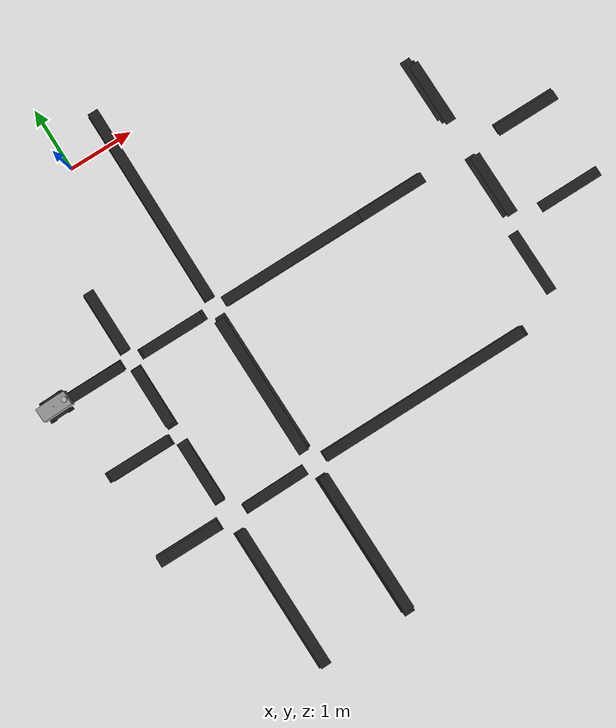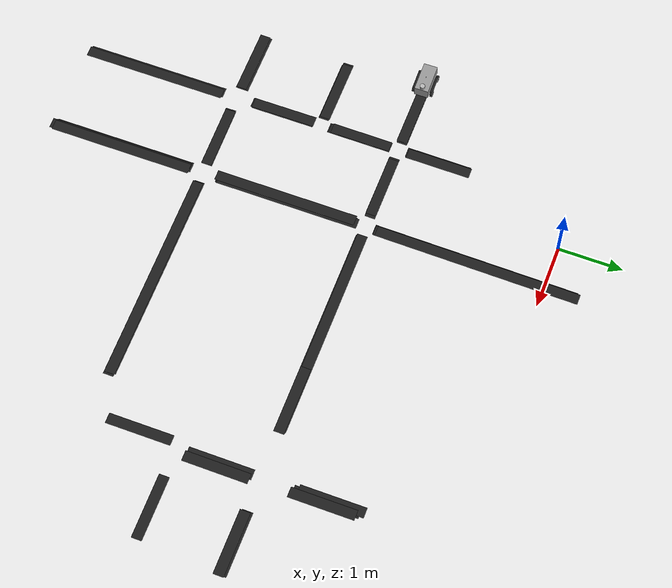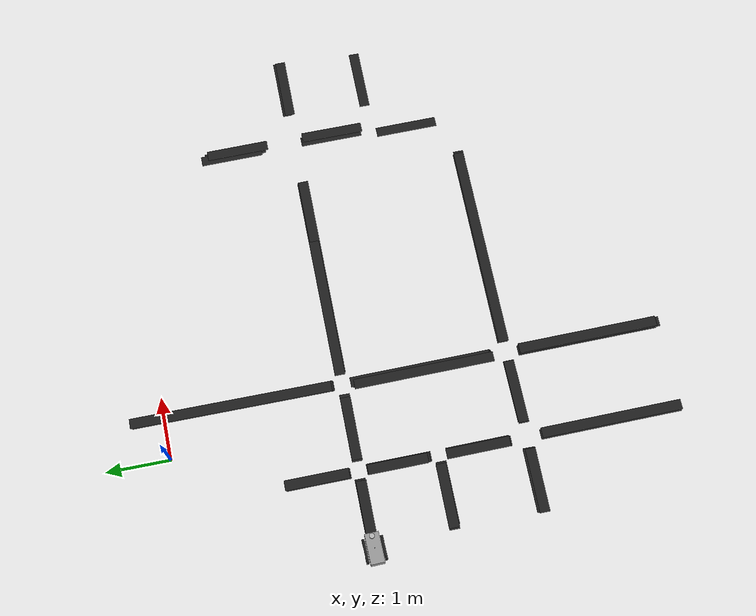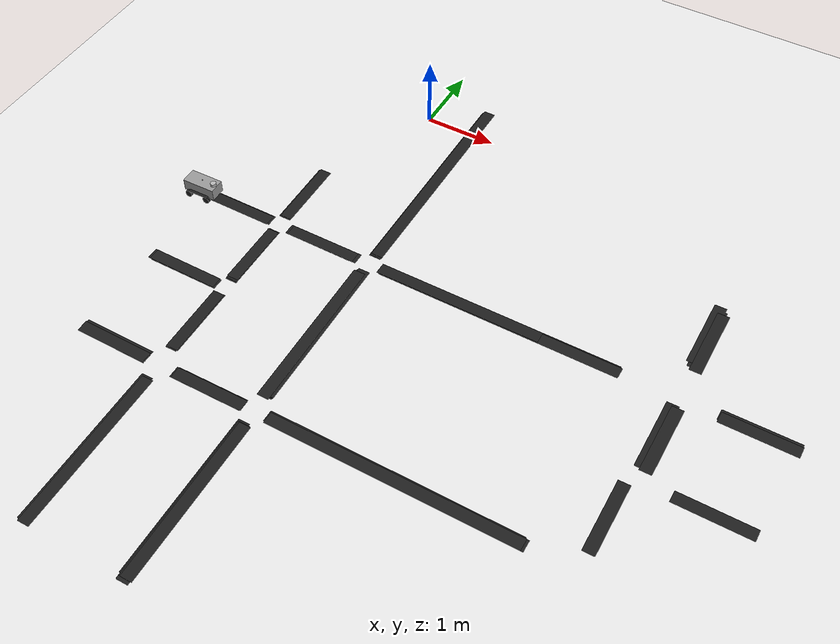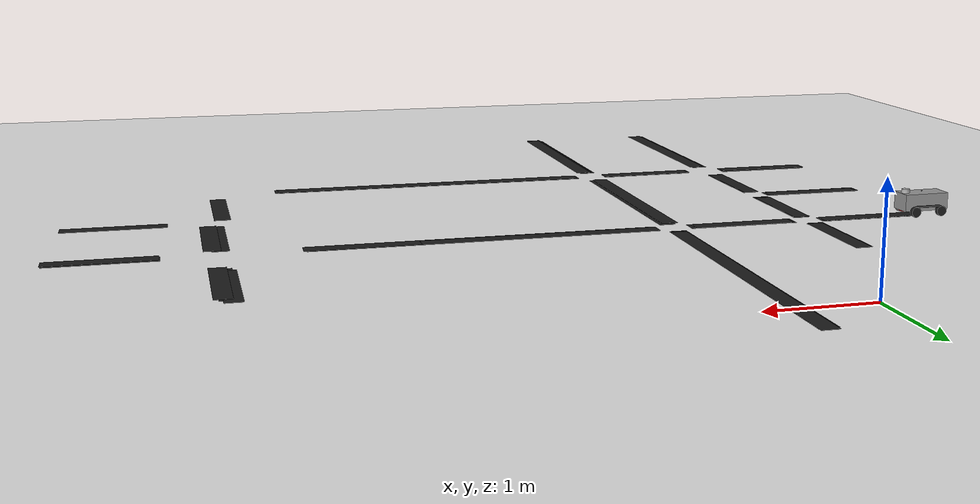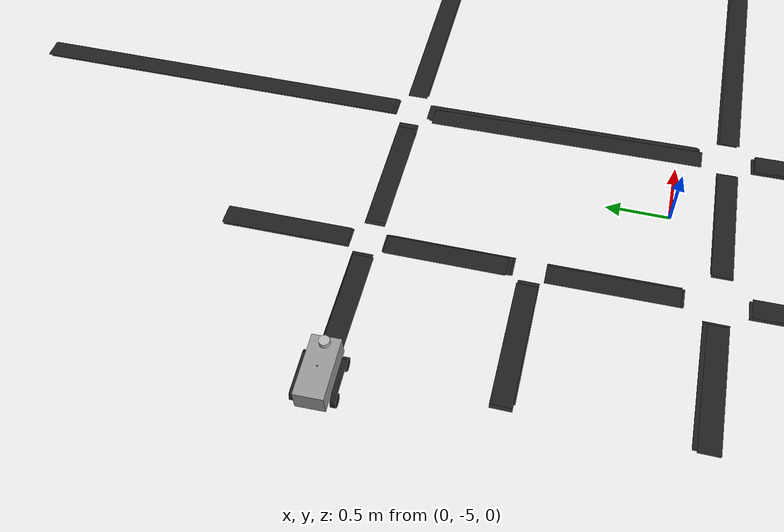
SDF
<sdf version="1.7">
 <world name="default">
  <light name="sun" type="directional">
   <pose>0 0 10 0 -0 0</pose>
   <diffuse>0.8 0.8 0.8 1</diffuse>
   <specular>0.2 0.2 0.2 1</specular>
   <attenuation>
    <range>1000</range>
    <constant>0.9</constant>
    <linear>0.01</linear>
    <quadratic>0.001</quadratic>
   </attenuation>
   <direction>-0.5 0.1 -0.9</direction>
   <spot><inner_angle>0</inner_angle><outer_angle>0</outer_angle><falloff>0</falloff></spot>
  </light>
  <model name="ground_plane">
   <static>1</static>
   <link name="link">
    <collision name="collision">
     <geometry><plane><normal>0 0 1</normal><size>100 100</size></plane></geometry>
     <surface>
      <contact><collide_bitmask>65535</collide_bitmask></contact>
      <friction><ode><mu>100</mu><mu2>50</mu2></ode></friction>
     </surface>
    </collision>
    <visual name="visual">
     <cast_shadows>0</cast_shadows>
     <geometry><plane><normal>0 0 1</normal><size>100 100</size></plane></geometry>
     <material>
      <script><uri>file://media/materials/scripts/gazebo.material</uri><name>Gazebo/White</name></script>
     </material>
    </visual>
   </link>
  </model>
  <model name="tankbot0">
   <pose>-1.9498 -2.79034 -1e-06 -2e-06 -3e-06 0.024518</pose>
   <frame name="tankbot::__model__" attached_to="tankbot::chassis">
    <pose relative_to="__model__">0 0 0 0 -0 0</pose>
   </frame>
   <link name="tankbot::chassis">
    <pose relative_to="tankbot::__model__">0 0 0.135 0 -0 0</pose>
    <inertial>
     <pose>0.0465 0 0 0 -0 0</pose>
     <mass>2</mass>
     <inertia>
      <ixx>0.0125927</ixx>
      <iyy>0.0408542</iyy>
      <izz>0.0438135</izz>
      <ixy>0</ixy>
      <ixz>0</ixz>
      <iyz>0</iyz>
     </inertia>
    </inertial>
    <collision name="collision"><geometry><box><size>0.465 0.216 0.17</size></box></geometry></collision>
    <visual name="visual">
     <geometry><box><size>0.465 0.216 0.17</size></box></geometry>
     <material>
      <script><uri>file://media/materials/scripts/gazebo.material</uri><name>Gazebo/Grey</name></script>
     </material>
    </visual>
   </link>
   <link name="tankbot::wheel_fl">
    <pose relative_to="tankbot::__model__">0.1395 0.142 0.05 -1.5708 -0.087266 0</pose>
    <inertial>
     <mass>0.25</mass>
     <inertia>
      <ixx>0.000189583</ixx>
      <iyy>0.000189583</iyy>
      <izz>0.0003125</izz>
      <ixy>0</ixy>
      <ixz>0</ixz>
      <iyz>0</iyz>
     </inertia>
    </inertial>
    <collision name="collision">
     <geometry><cylinder><radius>0.05</radius><length>0.04</length></cylinder></geometry>
    </collision>
    <visual name="tankbot::wheel_fl">
     <geometry><cylinder><radius>0.05</radius><length>0.04</length></cylinder></geometry>
     <material>
      <script><uri>file://media/materials/scripts/gazebo.material</uri><name>Gazebo/Black</name></script>
     </material>
    </visual>
   </link>
   <joint name="tankbot::wheel_fl_drive" type="revolute">
    <parent>tankbot::chassis</parent>
    <child>tankbot::wheel_fl</child>
    <axis>
     <xyz>0 0 1</xyz>
     <limit><lower>-1e+16</lower><upper>1e+16</upper></limit>
     <dynamics><spring_reference>0</spring_reference><spring_stiffness>0</spring_stiffness></dynamics>
    </axis>
   </joint>
   <link name="tankbot::chain_l_up">
    <pose relative_to="tankbot::__model__">0.0098 0.14 0.1 0 -0 0</pose>
    <gravity>0</gravity>
    <collision name="collision"><geometry><box><size>0.28 0.04 0.01</size></box></geometry></collision>
    <visual name="visual">
     <geometry><box><size>0.28 0.04 0.01</size></box></geometry>
     <material>
      <script><uri>file://media/materials/scripts/gazebo.material</uri><name>Gazebo/Black</name></script>
     </material>
    </visual>
    <inertial>
     <inertia><ixx>1</ixx><ixy>0</ixy><ixz>0</ixz><iyy>1</iyy><iyz>0</iyz><izz>1</izz></inertia>
     <mass>1</mass>
    </inertial>
   </link>
   <link name="tankbot::chain_r_up">
    <pose relative_to="tankbot::__model__">0.0098 -0.14 0.1 0 -0 0</pose>
    <gravity>0</gravity>
    <collision name="collision"><geometry><box><size>0.28 0.04 0.01</size></box></geometry></collision>
    <visual name="visual">
     <geometry><box><size>0.28 0.04 0.01</size></box></geometry>
     <material>
      <script><uri>file://media/materials/scripts/gazebo.material</uri><name>Gazebo/Black</name></script>
     </material>
    </visual>
    <inertial>
     <inertia><ixx>1</ixx><ixy>0</ixy><ixz>0</ixz><iyy>1</iyy><iyz>0</iyz><izz>1</izz></inertia>
     <mass>1</mass>
    </inertial>
   </link>
   <joint name="tankbot::chain_up_joint" type="revolute">
    <parent>tankbot::chassis</parent>
    <child>tankbot::chain_r_up</child>
   </joint>
   <joint name="tankbot::chain_up_2_joint" type="revolute">
    <parent>tankbot::chassis</parent>
    <child>tankbot::chain_l_up</child>
   </joint>
   <link name="tankbot::wheel_fr">
    <pose relative_to="tankbot::__model__">0.1395 -0.142 0.05 -1.5708 -0.087266 0</pose>
    <inertial>
     <mass>0.25</mass>
     <inertia>
      <ixx>0.000189583</ixx>
      <iyy>0.000189583</iyy>
      <izz>0.0003125</izz>
      <ixy>0</ixy>
      <ixz>0</ixz>
      <iyz>0</iyz>
     </inertia>
    </inertial>
    <collision name="collision">
     <geometry><cylinder><radius>0.05</radius><length>0.04</length></cylinder></geometry>
    </collision>
    <visual name="visual">
     <geometry><cylinder><radius>0.05</radius><length>0.04</length></cylinder></geometry>
     <material>
      <script><uri>file://media/materials/scripts/gazebo.material</uri><name>Gazebo/Black</name></script>
     </material>
    </visual>
   </link>
   <joint name="tankbot::wheel_fr_drive" type="revolute">
    <parent>tankbot::chassis</parent>
    <child>tankbot::wheel_fr</child>
    <axis>
     <xyz>0 0 1</xyz>
     <limit><lower>-1e+16</lower><upper>1e+16</upper></limit>
     <dynamics><spring_reference>0</spring_reference><spring_stiffness>0</spring_stiffness></dynamics>
    </axis>
   </joint>
   <link name="tankbot::wheel_rl">
    <pose relative_to="tankbot::__model__">-0.1395 0.142 0.05 -1.5708 0 0</pose>
    <inertial>
     <mass>0.25</mass>
     <inertia>
      <ixx>0.000189583</ixx>
      <iyy>0.000189583</iyy>
      <izz>0.0003125</izz>
      <ixy>0</ixy>
      <ixz>0</ixz>
      <iyz>0</iyz>
     </inertia>
    </inertial>
    <collision name="collision">
     <geometry><cylinder><radius>0</radius><length>0</length></cylinder></geometry>
    </collision>
    <visual name="visual">
     <geometry><cylinder><radius>0.05</radius><length>0.04</length></cylinder></geometry>
     <material>
      <script><uri>file://media/materials/scripts/gazebo.material</uri><name>Gazebo/Black</name></script>
     </material>
    </visual>
   </link>
   <joint name="tankbot::wheel_rl_drive" type="revolute">
    <parent>tankbot::chassis</parent>
    <child>tankbot::wheel_rl</child>
    <axis>
     <xyz>0 0 1</xyz>
     <limit><lower>-1e+16</lower><upper>1e+16</upper></limit>
     <dynamics><spring_reference>0</spring_reference><spring_stiffness>0</spring_stiffness></dynamics>
    </axis>
   </joint>
   <link name="tankbot::wheel_rr">
    <pose relative_to="tankbot::__model__">-0.1395 -0.142 0.05 -1.5708 0 0</pose>
    <inertial>
     <mass>0.25</mass>
     <inertia>
      <ixx>0.000189583</ixx>
      <iyy>0.000189583</iyy>
      <izz>0.0003125</izz>
      <ixy>0</ixy>
      <ixz>0</ixz>
      <iyz>0</iyz>
     </inertia>
    </inertial>
    <collision name="collision">
     <geometry><cylinder><radius>0.05</radius><length>0.04</length></cylinder></geometry>
    </collision>
    <visual name="visual">
     <geometry><cylinder><radius>0.05</radius><length>0.04</length></cylinder></geometry>
     <material>
      <script><uri>file://media/materials/scripts/gazebo.material</uri><name>Gazebo/Black</name></script>
     </material>
    </visual>
   </link>
   <joint name="tankbot::wheel_rr_drive" type="revolute">
    <parent>tankbot::chassis</parent>
    <child>tankbot::wheel_rr</child>
    <axis>
     <xyz>0 0 1</xyz>
     <limit><lower>-1e+16</lower><upper>1e+16</upper></limit>
     <dynamics><spring_reference>0</spring_reference><spring_stiffness>0</spring_stiffness></dynamics>
    </axis>
   </joint>
   <frame name="tankbot::ultrasonic_sensor::__model__" attached_to="tankbot::ultrasonic_sensor::link">
    <pose relative_to="tankbot::__model__">0.18 0 0.24 0 -0 0</pose>
   </frame>
   <link name="tankbot::ultrasonic_sensor::link">
    <inertial>
     <mass>0.1</mass>
     <inertia><ixx>1</ixx><ixy>0</ixy><ixz>0</ixz><iyy>1</iyy><iyz>0</iyz><izz>1</izz></inertia>
    </inertial>
    <visual name="visual">
     <geometry><cylinder><radius>0.04</radius><length>0.04</length></cylinder></geometry>
    </visual>
    <collision name="collision-base">
     <pose>0 0 -0.0145 0 -0 0</pose>
     <geometry><box><size>0.05 0.05 0.041</size></box></geometry>
    </collision>
    <collision name="collision-top">
     <pose>0 0 0.0205 0 -0 0</pose>
     <geometry><cylinder><radius>0.021</radius><length>0.029</length></cylinder></geometry>
    </collision>
    <sensor name="sonar" type="sonar">
     <pose>0.04 0 0 0 1.5 3.14</pose>
     <sonar><min>0</min><max>3</max><radius>0.3</radius></sonar>
     <plugin name="sonar" filename="libSonarPlugin.so"/>
     <always_on>1</always_on>
     <update_rate>30</update_rate>
     <visualize>1</visualize>
    </sensor>
    <pose relative_to="tankbot::ultrasonic_sensor::__model__">0 0 0 0 -0 0</pose>
   </link>
   <joint name="tankbot::sonar_joint" type="fixed">
    <child>tankbot::ultrasonic_sensor::link</child>
    <parent>tankbot::chassis</parent>
   </joint>
   <frame name="tankbot::camera_sensor::__model__" attached_to="tankbot::camera_sensor::link">
    <pose relative_to="tankbot::__model__">0.2 0 0.04 0 1.57 0</pose>
   </frame>
   <link name="tankbot::camera_sensor::link">
    <inertial>
     <mass>0.1</mass>
     <inertia><ixx>1</ixx><ixy>0</ixy><ixz>0</ixz><iyy>1</iyy><iyz>0</iyz><izz>1</izz></inertia>
    </inertial>
    <visual name="visual">
     <geometry><box><size>0.01 0.07 0.04</size></box></geometry>
     <material>
      <script><uri>file://media/materials/scripts/gazebo.material</uri><name>Gazebo/Red</name></script>
     </material>
    </visual>
    <collision name="collision">
     <pose>0 0 -0.0145 0 -0 0</pose>
     <geometry><box><size>0.01 0.07 0.04</size></box></geometry>
    </collision>
    <sensor name="camera" type="camera">
     <camera>
      <horizontal_fov>1.39626</horizontal_fov>
      <image><width>2</width><height>2</height></image>
      <clip><near>0.02</near><far>300</far></clip>
     </camera>
     <always_on>1</always_on>
     <update_rate>10</update_rate>
     <visualize>1</visualize>
     <plugin name="camera_controller" filename="libCameraPlugin.so"/>
    </sensor>
    <pose relative_to="tankbot::camera_sensor::__model__">0 0 0 0 -0 0</pose>
   </link>
   <frame name="tankbot::microphone_sensor::__model__" attached_to="tankbot::microphone_sensor::link">
    <pose relative_to="tankbot::__model__">0 0 0.23 0 -0 0</pose>
   </frame>
   <link name="tankbot::microphone_sensor::link">
    <inertial>
     <mass>0.1</mass>
     <inertia><ixx>1</ixx><ixy>0</ixy><ixz>0</ixz><iyy>1</iyy><iyz>0</iyz><izz>1</izz></inertia>
    </inertial>
    <visual name="visual">
     <geometry><box><size>0.01 0.01 0.01</size></box></geometry>
     <material>
      <script><uri>file://media/materials/scripts/gazebo.material</uri><name>Gazebo/Grey</name></script>
     </material>
    </visual>
    <collision name="collision"><geometry><box><size>0.01 0.01 0.01</size></box></geometry></collision>
    <pose relative_to="tankbot::microphone_sensor::__model__">0 0 0 0 -0 0</pose>
   </link>
   <plugin name="microphone_controller" filename="libmicrophone_control_plugin.so"/>
   <joint name="tankbot::camera_joint" type="fixed">
    <child>tankbot::camera_sensor::link</child>
    <parent>tankbot::chassis</parent>
   </joint>
   <plugin name="tankbot_control" filename="libtank_control_plugin.so"/>
   <plugin name="tankbot_control" filename="libtank_control_plugin.so"/>
  </model>
  <gravity>0 0 -9.8</gravity>
  <magnetic_field>6e-06 2.3e-05 -4.2e-05</magnetic_field>
  <atmosphere type="adiabatic"/>
  <physics type="ode">
   <max_step_size>0.001</max_step_size>
   <real_time_factor>1</real_time_factor>
   <real_time_update_rate>1000</real_time_update_rate>
  </physics>
  <scene><ambient>0.4 0.4 0.4 1</ambient><background>0.7 0.7 0.7 1</background><shadows>1</shadows></scene>
  <spherical_coordinates>
   <surface_model>EARTH_WGS84</surface_model>
   <latitude_deg>0</latitude_deg>
   <longitude_deg>0</longitude_deg>
   <elevation>0</elevation>
   <heading_deg>0</heading_deg>
  </spherical_coordinates>
  <model name="unit_box_clone_0_clone_clone_0">
   <link name="link">
    <inertial>
     <mass>1</mass>
     <inertia>
      <ixx>0.166667</ixx>
      <ixy>0</ixy>
      <ixz>0</ixz>
      <iyy>0.166667</iyy>
      <iyz>0</iyz>
      <izz>0.166667</izz>
     </inertia>
    </inertial>
    <visual name="visual">
     <geometry><box><size>1 0.160776 0.000937</size></box></geometry>
     <material>
      <script><name>Gazebo/Black</name><uri>file://media/materials/scripts/gazebo.material</uri></script>
      <shader type="pixel"><normal_map>__default__</normal_map></shader>
      <ambient>0 0 0 1</ambient>
      <diffuse>0 0 0 1</diffuse>
      <specular>0.1 0.1 0.1 1</specular>
      <emissive>0 0 0 1</emissive>
     </material>
    </visual>
    <collision name="collision">
     <geometry><box><size>1 0.160776 0.000937</size></box></geometry>
     <surface>
      <friction>
       <ode><mu>1</mu><mu2>1</mu2><fdir1>0 0 0</fdir1><slip1>0</slip1><slip2>0</slip2></ode>
       <torsional>
        <coefficient>1</coefficient>
        <patch_radius>0</patch_radius>
        <surface_radius>0</surface_radius>
        <use_patch_radius>1</use_patch_radius>
        <ode><slip>0</slip></ode>
       </torsional>
      </friction>
      <bounce><restitution_coefficient>0</restitution_coefficient><threshold>1e+06</threshold></bounce>
      <contact>
       <collide_without_contact>0</collide_without_contact>
       <collide_without_contact_bitmask>1</collide_without_contact_bitmask>
       <collide_bitmask>1</collide_bitmask>
       <ode>
        <soft_cfm>0</soft_cfm>
        <soft_erp>0.2</soft_erp>
        <kp>1e+13</kp>
        <kd>1</kd>
        <max_vel>0.01</max_vel>
        <min_depth>0</min_depth>
       </ode>
       <bullet>
        <split_impulse>1</split_impulse>
        <split_impulse_penetration_threshold>-0.01</split_impulse_penetration_threshold>
        <soft_cfm>0</soft_cfm>
        <soft_erp>0.2</soft_erp>
        <kp>1e+13</kp>
        <kd>1</kd>
       </bullet>
      </contact>
     </surface>
    </collision>
   </link>
   <static>0</static>
   <pose>0.00749 -2.7906 0.002011 6e-06 0.000285 -7.8e-05</pose>
  </model>
  <model name="unit_box_clone_0_clone_clone_clone_clone_clone_clone_clone_0_clone">
   <link name="link">
    <inertial>
     <mass>1</mass>
     <inertia>
      <ixx>0.166667</ixx>
      <ixy>0</ixy>
      <ixz>0</ixz>
      <iyy>0.166667</iyy>
      <iyz>0</iyz>
      <izz>0.166667</izz>
     </inertia>
    </inertial>
    <visual name="visual">
     <geometry><box><size>3.16167 0.161571 0.000937</size></box></geometry>
     <material>
      <script><name>Gazebo/Black</name><uri>file://media/materials/scripts/gazebo.material</uri></script>
      <shader type="pixel"><normal_map>__default__</normal_map></shader>
      <ambient>0 0 0 1</ambient>
      <diffuse>0 0 0 1</diffuse>
      <specular>0.1 0.1 0.1 1</specular>
      <emissive>0 0 0 1</emissive>
     </material>
    </visual>
    <collision name="collision">
     <geometry><box><size>3.16167 0.161571 0.000937</size></box></geometry>
     <surface>
      <friction>
       <ode><mu>1</mu><mu2>1</mu2><fdir1>0 0 0</fdir1><slip1>0</slip1><slip2>0</slip2></ode>
       <torsional>
        <coefficient>1</coefficient>
        <patch_radius>0</patch_radius>
        <surface_radius>0</surface_radius>
        <use_patch_radius>1</use_patch_radius>
        <ode><slip>0</slip></ode>
       </torsional>
      </friction>
      <bounce><restitution_coefficient>0</restitution_coefficient><threshold>1e+06</threshold></bounce>
      <contact>
       <collide_without_contact>0</collide_without_contact>
       <collide_without_contact_bitmask>1</collide_without_contact_bitmask>
       <collide_bitmask>1</collide_bitmask>
       <ode>
        <soft_cfm>0</soft_cfm>
        <soft_erp>0.2</soft_erp>
        <kp>1e+13</kp>
        <kd>1</kd>
        <max_vel>0.01</max_vel>
        <min_depth>0</min_depth>
       </ode>
       <bullet>
        <split_impulse>1</split_impulse>
        <split_impulse_penetration_threshold>-0.01</split_impulse_penetration_threshold>
        <soft_cfm>0</soft_cfm>
        <soft_erp>0.2</soft_erp>
        <kp>1e+13</kp>
        <kd>1</kd>
       </bullet>
      </contact>
     </surface>
    </collision>
   </link>
   <static>0</static>
   <pose>0.685812 -1.06745 -0.000124 -1.3e-05 -0.000376 -1.57339</pose>
  </model>
  <model name="unit_box_clone_0_clone_clone_0_clone_clone">
   <link name="link">
    <inertial>
     <mass>1</mass>
     <inertia>
      <ixx>0.166667</ixx>
      <ixy>0</ixy>
      <ixz>0</ixz>
      <iyy>0.166667</iyy>
      <iyz>0</iyz>
      <izz>0.166667</izz>
     </inertia>
    </inertial>
    <visual name="visual">
     <geometry><box><size>2.22866 0.160776 0.000937</size></box></geometry>
     <material>
      <script><name>Gazebo/Black</name><uri>file://media/materials/scripts/gazebo.material</uri></script>
      <shader type="pixel"><normal_map>__default__</normal_map></shader>
      <ambient>0 0 0 1</ambient>
      <diffuse>0 0 0 1</diffuse>
      <specular>0.1 0.1 0.1 1</specular>
      <emissive>0 0 0 1</emissive>
     </material>
    </visual>
    <collision name="collision">
     <geometry><box><size>2.22866 0.160776 0.000937</size></box></geometry>
     <surface>
      <friction>
       <ode><mu>1</mu><mu2>1</mu2><fdir1>0 0 0</fdir1><slip1>0</slip1><slip2>0</slip2></ode>
       <torsional>
        <coefficient>1</coefficient>
        <patch_radius>0</patch_radius>
        <surface_radius>0</surface_radius>
        <use_patch_radius>1</use_patch_radius>
        <ode><slip>0</slip></ode>
       </torsional>
      </friction>
      <bounce><restitution_coefficient>0</restitution_coefficient><threshold>1e+06</threshold></bounce>
      <contact>
       <collide_without_contact>0</collide_without_contact>
       <collide_without_contact_bitmask>1</collide_without_contact_bitmask>
       <collide_bitmask>1</collide_bitmask>
       <ode>
        <soft_cfm>0</soft_cfm>
        <soft_erp>0.2</soft_erp>
        <kp>1e+13</kp>
        <kd>1</kd>
        <max_vel>0.01</max_vel>
        <min_depth>0</min_depth>
       </ode>
       <bullet>
        <split_impulse>1</split_impulse>
        <split_impulse_penetration_threshold>-0.01</split_impulse_penetration_threshold>
        <soft_cfm>0</soft_cfm>
        <soft_erp>0.2</soft_erp>
        <kp>1e+13</kp>
        <kd>1</kd>
       </bullet>
      </contact>
     </surface>
    </collision>
   </link>
   <static>0</static>
   <pose>0.676438 -4.06335 0.000413 -0 -5e-05 -1.56233</pose>
  </model>
  <model name="unit_box_clone_0_clone_clone_0_clone_clone_clone">
   <link name="link">
    <inertial>
     <mass>1</mass>
     <inertia>
      <ixx>0.166667</ixx>
      <ixy>0</ixy>
      <ixz>0</ixz>
      <iyy>0.166667</iyy>
      <iyz>0</iyz>
      <izz>0.166667</izz>
     </inertia>
    </inertial>
    <visual name="visual">
     <geometry><box><size>1 0.160776 0.000937</size></box></geometry>
     <material>
      <script><name>Gazebo/Black</name><uri>file://media/materials/scripts/gazebo.material</uri></script>
      <shader type="pixel"><normal_map>__default__</normal_map></shader>
      <ambient>0 0 0 1</ambient>
      <diffuse>0 0 0 1</diffuse>
      <specular>0.1 0.1 0.1 1</specular>
      <emissive>0 0 0 1</emissive>
     </material>
    </visual>
    <collision name="collision">
     <geometry><box><size>1 0.160776 0.000937</size></box></geometry>
     <surface>
      <friction>
       <ode><mu>1</mu><mu2>1</mu2><fdir1>0 0 0</fdir1><slip1>0</slip1><slip2>0</slip2></ode>
       <torsional>
        <coefficient>1</coefficient>
        <patch_radius>0</patch_radius>
        <surface_radius>0</surface_radius>
        <use_patch_radius>1</use_patch_radius>
        <ode><slip>0</slip></ode>
       </torsional>
      </friction>
      <bounce><restitution_coefficient>0</restitution_coefficient><threshold>1e+06</threshold></bounce>
      <contact>
       <collide_without_contact>0</collide_without_contact>
       <collide_without_contact_bitmask>1</collide_without_contact_bitmask>
       <collide_bitmask>1</collide_bitmask>
       <ode>
        <soft_cfm>0</soft_cfm>
        <soft_erp>0.2</soft_erp>
        <kp>1e+13</kp>
        <kd>1</kd>
        <max_vel>0.01</max_vel>
        <min_depth>0</min_depth>
       </ode>
       <bullet>
        <split_impulse>1</split_impulse>
        <split_impulse_penetration_threshold>-0.01</split_impulse_penetration_threshold>
        <soft_cfm>0</soft_cfm>
        <soft_erp>0.2</soft_erp>
        <kp>1e+13</kp>
        <kd>1</kd>
       </bullet>
      </contact>
     </surface>
    </collision>
   </link>
   <static>0</static>
   <pose>4.8423 -4.65666 0.000468 -0 -0 -1.56222</pose>
  </model>
  <model name="unit_box_clone_0_clone_clone_0_clone_clone_0">
   <link name="link">
    <inertial>
     <mass>1</mass>
     <inertia>
      <ixx>0.166667</ixx>
      <ixy>0</ixy>
      <ixz>0</ixz>
      <iyy>0.166667</iyy>
      <iyz>0</iyz>
      <izz>0.166667</izz>
     </inertia>
    </inertial>
    <visual name="visual">
     <geometry><box><size>1 0.160776 0.000937</size></box></geometry>
     <material>
      <script><name>Gazebo/Black</name><uri>file://media/materials/scripts/gazebo.material</uri></script>
      <shader type="pixel"><normal_map>__default__</normal_map></shader>
      <ambient>0 0 0 1</ambient>
      <diffuse>0 0 0 1</diffuse>
      <specular>0.1 0.1 0.1 1</specular>
      <emissive>0 0 0 1</emissive>
     </material>
    </visual>
    <collision name="collision">
     <geometry><box><size>1 0.160776 0.000937</size></box></geometry>
     <surface>
      <friction>
       <ode><mu>1</mu><mu2>1</mu2><fdir1>0 0 0</fdir1><slip1>0</slip1><slip2>0</slip2></ode>
       <torsional>
        <coefficient>1</coefficient>
        <patch_radius>0</patch_radius>
        <surface_radius>0</surface_radius>
        <use_patch_radius>1</use_patch_radius>
        <ode><slip>0</slip></ode>
       </torsional>
      </friction>
      <bounce><restitution_coefficient>0</restitution_coefficient><threshold>1e+06</threshold></bounce>
      <contact>
       <collide_without_contact>0</collide_without_contact>
       <collide_without_contact_bitmask>1</collide_without_contact_bitmask>
       <collide_bitmask>1</collide_bitmask>
       <ode>
        <soft_cfm>0</soft_cfm>
        <soft_erp>0.2</soft_erp>
        <kp>1e+13</kp>
        <kd>1</kd>
        <max_vel>0.01</max_vel>
        <min_depth>0</min_depth>
       </ode>
       <bullet>
        <split_impulse>1</split_impulse>
        <split_impulse_penetration_threshold>-0.01</split_impulse_penetration_threshold>
        <soft_cfm>0</soft_cfm>
        <soft_erp>0.2</soft_erp>
        <kp>1e+13</kp>
        <kd>1</kd>
       </bullet>
      </contact>
     </surface>
    </collision>
   </link>
   <static>0</static>
   <pose>5.94297 -2.79646 0.001248 0 5.9e-05 -0.000883</pose>
  </model>
  <model name="unit_box_clone_0_clone_clone_0_clone_clone_clone_0">
   <link name="link">
    <inertial>
     <mass>1</mass>
     <inertia>
      <ixx>0.166667</ixx>
      <ixy>0</ixy>
      <ixz>0</ixz>
      <iyy>0.166667</iyy>
      <iyz>0</iyz>
      <izz>0.166667</izz>
     </inertia>
    </inertial>
    <visual name="visual">
     <geometry><box><size>1 0.160776 0.000937</size></box></geometry>
     <material>
      <script><name>Gazebo/Black</name><uri>file://media/materials/scripts/gazebo.material</uri></script>
      <shader type="pixel"><normal_map>__default__</normal_map></shader>
      <ambient>0 0 0 1</ambient>
      <diffuse>0 0 0 1</diffuse>
      <specular>0.1 0.1 0.1 1</specular>
      <emissive>0 0 0 1</emissive>
     </material>
    </visual>
    <collision name="collision">
     <geometry><box><size>1 0.160776 0.000937</size></box></geometry>
     <surface>
      <friction>
       <ode><mu>1</mu><mu2>1</mu2><fdir1>0 0 0</fdir1><slip1>0</slip1><slip2>0</slip2></ode>
       <torsional>
        <coefficient>1</coefficient>
        <patch_radius>0</patch_radius>
        <surface_radius>0</surface_radius>
        <use_patch_radius>1</use_patch_radius>
        <ode><slip>0</slip></ode>
       </torsional>
      </friction>
      <bounce><restitution_coefficient>0</restitution_coefficient><threshold>1e+06</threshold></bounce>
      <contact>
       <collide_without_contact>0</collide_without_contact>
       <collide_without_contact_bitmask>1</collide_without_contact_bitmask>
       <collide_bitmask>1</collide_bitmask>
       <ode>
        <soft_cfm>0</soft_cfm>
        <soft_erp>0.2</soft_erp>
        <kp>1e+13</kp>
        <kd>1</kd>
        <max_vel>0.01</max_vel>
        <min_depth>0</min_depth>
       </ode>
       <bullet>
        <split_impulse>1</split_impulse>
        <split_impulse_penetration_threshold>-0.01</split_impulse_penetration_threshold>
        <soft_cfm>0</soft_cfm>
        <soft_erp>0.2</soft_erp>
        <kp>1e+13</kp>
        <kd>1</kd>
       </bullet>
      </contact>
     </surface>
    </collision>
   </link>
   <static>0</static>
   <pose>4.88081 -1.72045 0.001388 -4e-06 4.1e-05 -1.56173</pose>
  </model>
  <model name="unit_box_clone_0_clone_clone_0_clone_0">
   <link name="link">
    <inertial>
     <mass>1</mass>
     <inertia>
      <ixx>0.166667</ixx>
      <ixy>0</ixy>
      <ixz>0</ixz>
      <iyy>0.166667</iyy>
      <iyz>0</iyz>
      <izz>0.166667</izz>
     </inertia>
    </inertial>
    <visual name="visual">
     <geometry><box><size>1 0.160776 0.000937</size></box></geometry>
     <material>
      <script><name>Gazebo/Black</name><uri>file://media/materials/scripts/gazebo.material</uri></script>
      <shader type="pixel"><normal_map>__default__</normal_map></shader>
      <ambient>0 0 0 1</ambient>
      <diffuse>0 0 0 1</diffuse>
      <specular>0.1 0.1 0.1 1</specular>
      <emissive>0 0 0 1</emissive>
     </material>
    </visual>
    <collision name="collision">
     <geometry><box><size>1 0.160776 0.000937</size></box></geometry>
     <surface>
      <friction>
       <ode><mu>1</mu><mu2>1</mu2><fdir1>0 0 0</fdir1><slip1>0</slip1><slip2>0</slip2></ode>
       <torsional>
        <coefficient>1</coefficient>
        <patch_radius>0</patch_radius>
        <surface_radius>0</surface_radius>
        <use_patch_radius>1</use_patch_radius>
        <ode><slip>0</slip></ode>
       </torsional>
      </friction>
      <bounce><restitution_coefficient>0</restitution_coefficient><threshold>1e+06</threshold></bounce>
      <contact>
       <collide_without_contact>0</collide_without_contact>
       <collide_without_contact_bitmask>1</collide_without_contact_bitmask>
       <collide_bitmask>1</collide_bitmask>
       <ode>
        <soft_cfm>0</soft_cfm>
        <soft_erp>0.2</soft_erp>
        <kp>1e+13</kp>
        <kd>1</kd>
        <max_vel>0.01</max_vel>
        <min_depth>0</min_depth>
       </ode>
       <bullet>
        <split_impulse>1</split_impulse>
        <split_impulse_penetration_threshold>-0.01</split_impulse_penetration_threshold>
        <soft_cfm>0</soft_cfm>
        <soft_erp>0.2</soft_erp>
        <kp>1e+13</kp>
        <kd>1</kd>
       </bullet>
      </contact>
     </surface>
    </collision>
   </link>
   <static>0</static>
   <pose>-1.37557 -2.78641 0.002186 1.6e-05 0.000206 -0.001155</pose>
  </model>
  <model name="unit_box_clone_0_clone_clone_0_clone_clone_clone_1">
   <link name="link">
    <inertial>
     <mass>1</mass>
     <inertia>
      <ixx>0.166667</ixx>
      <ixy>0</ixy>
      <ixz>0</ixz>
      <iyy>0.166667</iyy>
      <iyz>0</iyz>
      <izz>0.166667</izz>
     </inertia>
    </inertial>
    <visual name="visual">
     <geometry><box><size>1 0.160776 0.000937</size></box></geometry>
     <material>
      <script><name>Gazebo/Black</name><uri>file://media/materials/scripts/gazebo.material</uri></script>
      <shader type="pixel"><normal_map>__default__</normal_map></shader>
      <ambient>0 0 0 1</ambient>
      <diffuse>0 0 0 1</diffuse>
      <specular>0.1 0.1 0.1 1</specular>
      <emissive>0 0 0 1</emissive>
     </material>
    </visual>
    <collision name="collision">
     <geometry><box><size>1 0.160776 0.000937</size></box></geometry>
     <surface>
      <friction>
       <ode><mu>1</mu><mu2>1</mu2><fdir1>0 0 0</fdir1><slip1>0</slip1><slip2>0</slip2></ode>
       <torsional>
        <coefficient>1</coefficient>
        <patch_radius>0</patch_radius>
        <surface_radius>0</surface_radius>
        <use_patch_radius>1</use_patch_radius>
        <ode><slip>0</slip></ode>
       </torsional>
      </friction>
      <bounce><restitution_coefficient>0</restitution_coefficient><threshold>1e+06</threshold></bounce>
      <contact>
       <collide_without_contact>0</collide_without_contact>
       <collide_without_contact_bitmask>1</collide_without_contact_bitmask>
       <collide_bitmask>1</collide_bitmask>
       <ode>
        <soft_cfm>0</soft_cfm>
        <soft_erp>0.2</soft_erp>
        <kp>1e+13</kp>
        <kd>1</kd>
        <max_vel>0.01</max_vel>
        <min_depth>0</min_depth>
       </ode>
       <bullet>
        <split_impulse>1</split_impulse>
        <split_impulse_penetration_threshold>-0.01</split_impulse_penetration_threshold>
        <soft_cfm>0</soft_cfm>
        <soft_erp>0.2</soft_erp>
        <kp>1e+13</kp>
        <kd>1</kd>
       </bullet>
      </contact>
     </surface>
    </collision>
   </link>
   <static>0</static>
   <pose>-0.723755 -4.66652 0.000461 0 1.5e-05 -1.56225</pose>
  </model>
  <model name="unit_box_clone_0_clone_clone_0_clone_clone_clone_0_clone">
   <link name="link">
    <inertial>
     <mass>1</mass>
     <inertia>
      <ixx>0.166667</ixx>
      <ixy>0</ixy>
      <ixz>0</ixz>
      <iyy>0.166667</iyy>
      <iyz>0</iyz>
      <izz>0.166667</izz>
     </inertia>
    </inertial>
    <visual name="visual">
     <geometry><box><size>1 0.160776 0.000937</size></box></geometry>
     <material>
      <script><name>Gazebo/Black</name><uri>file://media/materials/scripts/gazebo.material</uri></script>
      <shader type="pixel"><normal_map>__default__</normal_map></shader>
      <ambient>0 0 0 1</ambient>
      <diffuse>0 0 0 1</diffuse>
      <specular>0.1 0.1 0.1 1</specular>
      <emissive>0 0 0 1</emissive>
     </material>
    </visual>
    <collision name="collision">
     <geometry><box><size>1 0.160776 0.000937</size></box></geometry>
     <surface>
      <friction>
       <ode><mu>1</mu><mu2>1</mu2><fdir1>0 0 0</fdir1><slip1>0</slip1><slip2>0</slip2></ode>
       <torsional>
        <coefficient>1</coefficient>
        <patch_radius>0</patch_radius>
        <surface_radius>0</surface_radius>
        <use_patch_radius>1</use_patch_radius>
        <ode><slip>0</slip></ode>
       </torsional>
      </friction>
      <bounce><restitution_coefficient>0</restitution_coefficient><threshold>1e+06</threshold></bounce>
      <contact>
       <collide_without_contact>0</collide_without_contact>
       <collide_without_contact_bitmask>1</collide_without_contact_bitmask>
       <collide_bitmask>1</collide_bitmask>
       <ode>
        <soft_cfm>0</soft_cfm>
        <soft_erp>0.2</soft_erp>
        <kp>1e+13</kp>
        <kd>1</kd>
        <max_vel>0.01</max_vel>
        <min_depth>0</min_depth>
       </ode>
       <bullet>
        <split_impulse>1</split_impulse>
        <split_impulse_penetration_threshold>-0.01</split_impulse_penetration_threshold>
        <soft_cfm>0</soft_cfm>
        <soft_erp>0.2</soft_erp>
        <kp>1e+13</kp>
        <kd>1</kd>
       </bullet>
      </contact>
     </surface>
    </collision>
   </link>
   <static>0</static>
   <pose>-0.725916 -2.13603 0.002308 -4e-06 -6.7e-05 -1.56699</pose>
  </model>
  <model name="unit_box_clone_0_clone_clone_0_clone_1">
   <link name="link">
    <inertial>
     <mass>1</mass>
     <inertia>
      <ixx>0.166667</ixx>
      <ixy>0</ixy>
      <ixz>0</ixz>
      <iyy>0.166667</iyy>
      <iyz>0</iyz>
      <izz>0.166667</izz>
     </inertia>
    </inertial>
    <visual name="visual">
     <geometry><box><size>1 0.160776 0.000937</size></box></geometry>
     <material>
      <script><name>Gazebo/Black</name><uri>file://media/materials/scripts/gazebo.material</uri></script>
      <shader type="pixel"><normal_map>__default__</normal_map></shader>
      <ambient>0 0 0 1</ambient>
      <diffuse>0 0 0 1</diffuse>
      <specular>0.1 0.1 0.1 1</specular>
      <emissive>0 0 0 1</emissive>
     </material>
    </visual>
    <collision name="collision">
     <geometry><box><size>1 0.160776 0.000937</size></box></geometry>
     <surface>
      <friction>
       <ode><mu>1</mu><mu2>1</mu2><fdir1>0 0 0</fdir1><slip1>0</slip1><slip2>0</slip2></ode>
       <torsional>
        <coefficient>1</coefficient>
        <patch_radius>0</patch_radius>
        <surface_radius>0</surface_radius>
        <use_patch_radius>1</use_patch_radius>
        <ode><slip>0</slip></ode>
       </torsional>
      </friction>
      <bounce><restitution_coefficient>0</restitution_coefficient><threshold>1e+06</threshold></bounce>
      <contact>
       <collide_without_contact>0</collide_without_contact>
       <collide_without_contact_bitmask>1</collide_without_contact_bitmask>
       <collide_bitmask>1</collide_bitmask>
       <ode>
        <soft_cfm>0</soft_cfm>
        <soft_erp>0.2</soft_erp>
        <kp>1e+13</kp>
        <kd>1</kd>
        <max_vel>0.01</max_vel>
        <min_depth>0</min_depth>
       </ode>
       <bullet>
        <split_impulse>1</split_impulse>
        <split_impulse_penetration_threshold>-0.01</split_impulse_penetration_threshold>
        <soft_cfm>0</soft_cfm>
        <soft_erp>0.2</soft_erp>
        <kp>1e+13</kp>
        <kd>1</kd>
       </bullet>
      </contact>
     </surface>
    </collision>
   </link>
   <static>0</static>
   <pose>0.039276 -5.41097 0.000324 5e-06 0.000288 0.011983</pose>
  </model>
  <model name="unit_box_clone_0_clone_clone_0_clone_clone_0_clone">
   <link name="link">
    <inertial>
     <mass>1</mass>
     <inertia>
      <ixx>0.166667</ixx>
      <ixy>0</ixy>
      <ixz>0</ixz>
      <iyy>0.166667</iyy>
      <iyz>0</iyz>
      <izz>0.166667</izz>
     </inertia>
    </inertial>
    <visual name="visual">
     <geometry><box><size>1 0.160776 0.000937</size></box></geometry>
     <material>
      <script><name>Gazebo/Black</name><uri>file://media/materials/scripts/gazebo.material</uri></script>
      <shader type="pixel"><normal_map>__default__</normal_map></shader>
      <ambient>0 0 0 1</ambient>
      <diffuse>0 0 0 1</diffuse>
      <specular>0.1 0.1 0.1 1</specular>
      <emissive>0 0 0 1</emissive>
     </material>
    </visual>
    <collision name="collision">
     <geometry><box><size>1 0.160776 0.000937</size></box></geometry>
     <surface>
      <friction>
       <ode><mu>1</mu><mu2>1</mu2><fdir1>0 0 0</fdir1><slip1>0</slip1><slip2>0</slip2></ode>
       <torsional>
        <coefficient>1</coefficient>
        <patch_radius>0</patch_radius>
        <surface_radius>0</surface_radius>
        <use_patch_radius>1</use_patch_radius>
        <ode><slip>0</slip></ode>
       </torsional>
      </friction>
      <bounce><restitution_coefficient>0</restitution_coefficient><threshold>1e+06</threshold></bounce>
      <contact>
       <collide_without_contact>0</collide_without_contact>
       <collide_without_contact_bitmask>1</collide_without_contact_bitmask>
       <collide_bitmask>1</collide_bitmask>
       <ode>
        <soft_cfm>0</soft_cfm>
        <soft_erp>0.2</soft_erp>
        <kp>1e+13</kp>
        <kd>1</kd>
        <max_vel>0.01</max_vel>
        <min_depth>0</min_depth>
       </ode>
       <bullet>
        <split_impulse>1</split_impulse>
        <split_impulse_penetration_threshold>-0.01</split_impulse_penetration_threshold>
        <soft_cfm>0</soft_cfm>
        <soft_erp>0.2</soft_erp>
        <kp>1e+13</kp>
        <kd>1</kd>
       </bullet>
      </contact>
     </surface>
    </collision>
   </link>
   <static>0</static>
   <pose>5.8624 -4.05427 0.000466 0 5e-06 0.000248</pose>
  </model>
  <model name="unit_box_clone_0_clone_clone_0_clone_clone_clone_2_clone">
   <link name="link">
    <inertial>
     <mass>1</mass>
     <inertia>
      <ixx>0.166667</ixx>
      <ixy>0</ixy>
      <ixz>0</ixz>
      <iyy>0.166667</iyy>
      <iyz>0</iyz>
      <izz>0.166667</izz>
     </inertia>
    </inertial>
    <visual name="visual">
     <geometry><box><size>1 0.160776 0.000937</size></box></geometry>
     <material>
      <script><name>Gazebo/Black</name><uri>file://media/materials/scripts/gazebo.material</uri></script>
      <shader type="pixel"><normal_map>__default__</normal_map></shader>
      <ambient>0 0 0 1</ambient>
      <diffuse>0 0 0 1</diffuse>
      <specular>0.1 0.1 0.1 1</specular>
      <emissive>0 0 0 1</emissive>
     </material>
    </visual>
    <collision name="collision">
     <geometry><box><size>1 0.160776 0.000937</size></box></geometry>
     <surface>
      <friction>
       <ode><mu>1</mu><mu2>1</mu2><fdir1>0 0 0</fdir1><slip1>0</slip1><slip2>0</slip2></ode>
       <torsional>
        <coefficient>1</coefficient>
        <patch_radius>0</patch_radius>
        <surface_radius>0</surface_radius>
        <use_patch_radius>1</use_patch_radius>
        <ode><slip>0</slip></ode>
       </torsional>
      </friction>
      <bounce><restitution_coefficient>0</restitution_coefficient><threshold>1e+06</threshold></bounce>
      <contact>
       <collide_without_contact>0</collide_without_contact>
       <collide_without_contact_bitmask>1</collide_without_contact_bitmask>
       <collide_bitmask>1</collide_bitmask>
       <ode>
        <soft_cfm>0</soft_cfm>
        <soft_erp>0.2</soft_erp>
        <kp>1e+13</kp>
        <kd>1</kd>
        <max_vel>0.01</max_vel>
        <min_depth>0</min_depth>
       </ode>
       <bullet>
        <split_impulse>1</split_impulse>
        <split_impulse_penetration_threshold>-0.01</split_impulse_penetration_threshold>
        <soft_cfm>0</soft_cfm>
        <soft_erp>0.2</soft_erp>
        <kp>1e+13</kp>
        <kd>1</kd>
       </bullet>
      </contact>
     </surface>
    </collision>
   </link>
   <static>0</static>
   <pose>-0.719245 -3.40895 0.000468 2e-06 1e-06 -1.56566</pose>
  </model>
  <model name="unit_box_clone_0_clone_clone_0_clone_1_clone">
   <link name="link">
    <inertial>
     <mass>1</mass>
     <inertia>
      <ixx>0.166667</ixx>
      <ixy>0</ixy>
      <ixz>0</ixz>
      <iyy>0.166667</iyy>
      <iyz>0</iyz>
      <izz>0.166667</izz>
     </inertia>
    </inertial>
    <visual name="visual">
     <geometry><box><size>1 0.160776 0.000937</size></box></geometry>
     <material>
      <script><name>Gazebo/Black</name><uri>file://media/materials/scripts/gazebo.material</uri></script>
      <shader type="pixel"><normal_map>__default__</normal_map></shader>
      <ambient>0 0 0 1</ambient>
      <diffuse>0 0 0 1</diffuse>
      <specular>0.1 0.1 0.1 1</specular>
      <emissive>0 0 0 1</emissive>
     </material>
    </visual>
    <collision name="collision">
     <geometry><box><size>1 0.160776 0.000937</size></box></geometry>
     <surface>
      <friction>
       <ode><mu>1</mu><mu2>1</mu2><fdir1>0 0 0</fdir1><slip1>0</slip1><slip2>0</slip2></ode>
       <torsional>
        <coefficient>1</coefficient>
        <patch_radius>0</patch_radius>
        <surface_radius>0</surface_radius>
        <use_patch_radius>1</use_patch_radius>
        <ode><slip>0</slip></ode>
       </torsional>
      </friction>
      <bounce><restitution_coefficient>0</restitution_coefficient><threshold>1e+06</threshold></bounce>
      <contact>
       <collide_without_contact>0</collide_without_contact>
       <collide_without_contact_bitmask>1</collide_without_contact_bitmask>
       <collide_bitmask>1</collide_bitmask>
       <ode>
        <soft_cfm>0</soft_cfm>
        <soft_erp>0.2</soft_erp>
        <kp>1e+13</kp>
        <kd>1</kd>
        <max_vel>0.01</max_vel>
        <min_depth>0</min_depth>
       </ode>
       <bullet>
        <split_impulse>1</split_impulse>
        <split_impulse_penetration_threshold>-0.01</split_impulse_penetration_threshold>
        <soft_cfm>0</soft_cfm>
        <soft_erp>0.2</soft_erp>
        <kp>1e+13</kp>
        <kd>1</kd>
       </bullet>
      </contact>
     </surface>
    </collision>
   </link>
   <static>0</static>
   <pose>-1.38089 -4.03194 0.000409 0 0.000119 -0.004304</pose>
  </model>
  <model name="unit_box_clone_0_clone_clone_0_clone_0_clone">
   <link name="link">
    <inertial>
     <mass>1</mass>
     <inertia>
      <ixx>0.166667</ixx>
      <ixy>0</ixy>
      <ixz>0</ixz>
      <iyy>0.166667</iyy>
      <iyz>0</iyz>
      <izz>0.166667</izz>
     </inertia>
    </inertial>
    <visual name="visual">
     <geometry><box><size>1 0.160776 0.000937</size></box></geometry>
     <material>
      <script><name>Gazebo/Black</name><uri>file://media/materials/scripts/gazebo.material</uri></script>
      <shader type="pixel"><normal_map>__default__</normal_map></shader>
      <ambient>0 0 0 1</ambient>
      <diffuse>0 0 0 1</diffuse>
      <specular>0.1 0.1 0.1 1</specular>
      <emissive>0 0 0 1</emissive>
     </material>
    </visual>
    <collision name="collision">
     <geometry><box><size>1 0.160776 0.000937</size></box></geometry>
     <surface>
      <friction>
       <ode><mu>1</mu><mu2>1</mu2><fdir1>0 0 0</fdir1><slip1>0</slip1><slip2>0</slip2></ode>
       <torsional>
        <coefficient>1</coefficient>
        <patch_radius>0</patch_radius>
        <surface_radius>0</surface_radius>
        <use_patch_radius>1</use_patch_radius>
        <ode><slip>0</slip></ode>
       </torsional>
      </friction>
      <bounce><restitution_coefficient>0</restitution_coefficient><threshold>1e+06</threshold></bounce>
      <contact>
       <collide_without_contact>0</collide_without_contact>
       <collide_without_contact_bitmask>1</collide_without_contact_bitmask>
       <collide_bitmask>1</collide_bitmask>
       <ode>
        <soft_cfm>0</soft_cfm>
        <soft_erp>0.2</soft_erp>
        <kp>1e+13</kp>
        <kd>1</kd>
        <max_vel>0.01</max_vel>
        <min_depth>0</min_depth>
       </ode>
       <bullet>
        <split_impulse>1</split_impulse>
        <split_impulse_penetration_threshold>-0.01</split_impulse_penetration_threshold>
        <soft_cfm>0</soft_cfm>
        <soft_erp>0.2</soft_erp>
        <kp>1e+13</kp>
        <kd>1</kd>
       </bullet>
      </contact>
     </surface>
    </collision>
   </link>
   <static>0</static>
   <pose>-1.37532 -2.78313 0.001257 1.7e-05 0.00019 0.002011</pose>
  </model>
  <model name="unit_box_clone_0_clone_clone_0_clone_0_clone_0">
   <link name="link">
    <inertial>
     <mass>1</mass>
     <inertia>
      <ixx>0.166667</ixx>
      <ixy>0</ixy>
      <ixz>0</ixz>
      <iyy>0.166667</iyy>
      <iyz>0</iyz>
      <izz>0.166667</izz>
     </inertia>
    </inertial>
    <visual name="visual">
     <geometry><box><size>1 0.160776 0.000937</size></box></geometry>
     <material>
      <script><name>Gazebo/Black</name><uri>file://media/materials/scripts/gazebo.material</uri></script>
      <shader type="pixel"><normal_map>__default__</normal_map></shader>
      <ambient>0 0 0 1</ambient>
      <diffuse>0 0 0 1</diffuse>
      <specular>0.1 0.1 0.1 1</specular>
      <emissive>0 0 0 1</emissive>
     </material>
    </visual>
    <collision name="collision">
     <geometry><box><size>1 0.160776 0.000937</size></box></geometry>
     <surface>
      <friction>
       <ode><mu>1</mu><mu2>1</mu2><fdir1>0 0 0</fdir1><slip1>0</slip1><slip2>0</slip2></ode>
       <torsional>
        <coefficient>1</coefficient>
        <patch_radius>0</patch_radius>
        <surface_radius>0</surface_radius>
        <use_patch_radius>1</use_patch_radius>
        <ode><slip>0</slip></ode>
       </torsional>
      </friction>
      <bounce><restitution_coefficient>0</restitution_coefficient><threshold>1e+06</threshold></bounce>
      <contact>
       <collide_without_contact>0</collide_without_contact>
       <collide_without_contact_bitmask>1</collide_without_contact_bitmask>
       <collide_bitmask>1</collide_bitmask>
       <ode>
        <soft_cfm>0</soft_cfm>
        <soft_erp>0.2</soft_erp>
        <kp>1e+13</kp>
        <kd>1</kd>
        <max_vel>0.01</max_vel>
        <min_depth>0</min_depth>
       </ode>
       <bullet>
        <split_impulse>1</split_impulse>
        <split_impulse_penetration_threshold>-0.01</split_impulse_penetration_threshold>
        <soft_cfm>0</soft_cfm>
        <soft_erp>0.2</soft_erp>
        <kp>1e+13</kp>
        <kd>1</kd>
       </bullet>
      </contact>
     </surface>
    </collision>
   </link>
   <static>0</static>
   <pose>-1.34736 -2.77733 0.000441 0 -5.4e-05 0.001725</pose>
  </model>
  <model name="unit_box_clone_0_clone_clone_0_clone_0_clone_1">
   <link name="link">
    <inertial>
     <mass>1</mass>
     <inertia>
      <ixx>0.166667</ixx>
      <ixy>0</ixy>
      <ixz>0</ixz>
      <iyy>0.166667</iyy>
      <iyz>0</iyz>
      <izz>0.166667</izz>
     </inertia>
    </inertial>
    <visual name="visual">
     <geometry><box><size>1 0.160776 0.000937</size></box></geometry>
     <material>
      <script><name>Gazebo/Black</name><uri>file://media/materials/scripts/gazebo.material</uri></script>
      <shader type="pixel"><normal_map>__default__</normal_map></shader>
      <ambient>0 0 0 1</ambient>
      <diffuse>0 0 0 1</diffuse>
      <specular>0.1 0.1 0.1 1</specular>
      <emissive>0 0 0 1</emissive>
     </material>
    </visual>
    <collision name="collision">
     <geometry><box><size>1 0.160776 0.000937</size></box></geometry>
     <surface>
      <friction>
       <ode><mu>1</mu><mu2>1</mu2><fdir1>0 0 0</fdir1><slip1>0</slip1><slip2>0</slip2></ode>
       <torsional>
        <coefficient>1</coefficient>
        <patch_radius>0</patch_radius>
        <surface_radius>0</surface_radius>
        <use_patch_radius>1</use_patch_radius>
        <ode><slip>0</slip></ode>
       </torsional>
      </friction>
      <bounce><restitution_coefficient>0</restitution_coefficient><threshold>1e+06</threshold></bounce>
      <contact>
       <collide_without_contact>0</collide_without_contact>
       <collide_without_contact_bitmask>1</collide_without_contact_bitmask>
       <collide_bitmask>1</collide_bitmask>
       <ode>
        <soft_cfm>0</soft_cfm>
        <soft_erp>0.2</soft_erp>
        <kp>1e+13</kp>
        <kd>1</kd>
        <max_vel>0.01</max_vel>
        <min_depth>0</min_depth>
       </ode>
       <bullet>
        <split_impulse>1</split_impulse>
        <split_impulse_penetration_threshold>-0.01</split_impulse_penetration_threshold>
        <soft_cfm>0</soft_cfm>
        <soft_erp>0.2</soft_erp>
        <kp>1e+13</kp>
        <kd>1</kd>
       </bullet>
      </contact>
     </surface>
    </collision>
   </link>
   <static>0</static>
   <pose>-0.042138 -2.79182 0.002853 8e-06 6.7e-05 0.000469</pose>
  </model>
  <model name="unit_box_clone_0_clone_clone_0_clone_0_clone_2">
   <link name="link">
    <inertial>
     <mass>1</mass>
     <inertia>
      <ixx>0.166667</ixx>
      <ixy>0</ixy>
      <ixz>0</ixz>
      <iyy>0.166667</iyy>
      <iyz>0</iyz>
      <izz>0.166667</izz>
     </inertia>
    </inertial>
    <visual name="visual">
     <geometry><box><size>1 0.160776 0.000937</size></box></geometry>
     <material>
      <script><name>Gazebo/Black</name><uri>file://media/materials/scripts/gazebo.material</uri></script>
      <shader type="pixel"><normal_map>__default__</normal_map></shader>
      <ambient>0 0 0 1</ambient>
      <diffuse>0 0 0 1</diffuse>
      <specular>0.1 0.1 0.1 1</specular>
      <emissive>0 0 0 1</emissive>
     </material>
    </visual>
    <collision name="collision">
     <geometry><box><size>1 0.160776 0.000937</size></box></geometry>
     <surface>
      <friction>
       <ode><mu>1</mu><mu2>1</mu2><fdir1>0 0 0</fdir1><slip1>0</slip1><slip2>0</slip2></ode>
       <torsional>
        <coefficient>1</coefficient>
        <patch_radius>0</patch_radius>
        <surface_radius>0</surface_radius>
        <use_patch_radius>1</use_patch_radius>
        <ode><slip>0</slip></ode>
       </torsional>
      </friction>
      <bounce><restitution_coefficient>0</restitution_coefficient><threshold>1e+06</threshold></bounce>
      <contact>
       <collide_without_contact>0</collide_without_contact>
       <collide_without_contact_bitmask>1</collide_without_contact_bitmask>
       <collide_bitmask>1</collide_bitmask>
       <ode>
        <soft_cfm>0</soft_cfm>
        <soft_erp>0.2</soft_erp>
        <kp>1e+13</kp>
        <kd>1</kd>
        <max_vel>0.01</max_vel>
        <min_depth>0</min_depth>
       </ode>
       <bullet>
        <split_impulse>1</split_impulse>
        <split_impulse_penetration_threshold>-0.01</split_impulse_penetration_threshold>
        <soft_cfm>0</soft_cfm>
        <soft_erp>0.2</soft_erp>
        <kp>1e+13</kp>
        <kd>1</kd>
       </bullet>
      </contact>
     </surface>
    </collision>
   </link>
   <static>0</static>
   <pose>-0.026069 -2.79162 0.001312 4e-06 -0.000206 -0.001029</pose>
  </model>
  <model name="unit_box_clone_0_clone_clone_0_clone_0_clone_3">
   <link name="link">
    <inertial>
     <mass>1</mass>
     <inertia>
      <ixx>0.166667</ixx>
      <ixy>0</ixy>
      <ixz>0</ixz>
      <iyy>0.166667</iyy>
      <iyz>0</iyz>
      <izz>0.166667</izz>
     </inertia>
    </inertial>
    <visual name="visual">
     <geometry><box><size>1 0.160776 0.000937</size></box></geometry>
     <material>
      <script><name>Gazebo/Black</name><uri>file://media/materials/scripts/gazebo.material</uri></script>
      <shader type="pixel"><normal_map>__default__</normal_map></shader>
      <ambient>0 0 0 1</ambient>
      <diffuse>0 0 0 1</diffuse>
      <specular>0.1 0.1 0.1 1</specular>
      <emissive>0 0 0 1</emissive>
     </material>
    </visual>
    <collision name="collision">
     <geometry><box><size>1 0.160776 0.000937</size></box></geometry>
     <surface>
      <friction>
       <ode><mu>1</mu><mu2>1</mu2><fdir1>0 0 0</fdir1><slip1>0</slip1><slip2>0</slip2></ode>
       <torsional>
        <coefficient>1</coefficient>
        <patch_radius>0</patch_radius>
        <surface_radius>0</surface_radius>
        <use_patch_radius>1</use_patch_radius>
        <ode><slip>0</slip></ode>
       </torsional>
      </friction>
      <bounce><restitution_coefficient>0</restitution_coefficient><threshold>1e+06</threshold></bounce>
      <contact>
       <collide_without_contact>0</collide_without_contact>
       <collide_without_contact_bitmask>1</collide_without_contact_bitmask>
       <collide_bitmask>1</collide_bitmask>
       <ode>
        <soft_cfm>0</soft_cfm>
        <soft_erp>0.2</soft_erp>
        <kp>1e+13</kp>
        <kd>1</kd>
        <max_vel>0.01</max_vel>
        <min_depth>0</min_depth>
       </ode>
       <bullet>
        <split_impulse>1</split_impulse>
        <split_impulse_penetration_threshold>-0.01</split_impulse_penetration_threshold>
        <soft_cfm>0</soft_cfm>
        <soft_erp>0.2</soft_erp>
        <kp>1e+13</kp>
        <kd>1</kd>
       </bullet>
      </contact>
     </surface>
    </collision>
   </link>
   <static>0</static>
   <pose>-0.073142 -2.79257 0.000468 2e-06 0 -0.004545</pose>
  </model>
  <model name="unit_box_clone_0_clone_clone_0_clone_clone_clone_2_clone_clone_1">
   <link name="link">
    <inertial>
     <mass>1</mass>
     <inertia>
      <ixx>0.166667</ixx>
      <ixy>0</ixy>
      <ixz>0</ixz>
      <iyy>0.166667</iyy>
      <iyz>0</iyz>
      <izz>0.166667</izz>
     </inertia>
    </inertial>
    <visual name="visual">
     <geometry><box><size>1 0.160776 0.000937</size></box></geometry>
     <material>
      <script><name>Gazebo/Black</name><uri>file://media/materials/scripts/gazebo.material</uri></script>
      <shader type="pixel"><normal_map>__default__</normal_map></shader>
      <ambient>0 0 0 1</ambient>
      <diffuse>0 0 0 1</diffuse>
      <specular>0.1 0.1 0.1 1</specular>
      <emissive>0 0 0 1</emissive>
     </material>
    </visual>
    <collision name="collision">
     <geometry><box><size>1 0.160776 0.000937</size></box></geometry>
     <surface>
      <friction>
       <ode><mu>1</mu><mu2>1</mu2><fdir1>0 0 0</fdir1><slip1>0</slip1><slip2>0</slip2></ode>
       <torsional>
        <coefficient>1</coefficient>
        <patch_radius>0</patch_radius>
        <surface_radius>0</surface_radius>
        <use_patch_radius>1</use_patch_radius>
        <ode><slip>0</slip></ode>
       </torsional>
      </friction>
      <bounce><restitution_coefficient>0</restitution_coefficient><threshold>1e+06</threshold></bounce>
      <contact>
       <collide_without_contact>0</collide_without_contact>
       <collide_without_contact_bitmask>1</collide_without_contact_bitmask>
       <collide_bitmask>1</collide_bitmask>
       <ode>
        <soft_cfm>0</soft_cfm>
        <soft_erp>0.2</soft_erp>
        <kp>1e+13</kp>
        <kd>1</kd>
        <max_vel>0.01</max_vel>
        <min_depth>0</min_depth>
       </ode>
       <bullet>
        <split_impulse>1</split_impulse>
        <split_impulse_penetration_threshold>-0.01</split_impulse_penetration_threshold>
        <soft_cfm>0</soft_cfm>
        <soft_erp>0.2</soft_erp>
        <kp>1e+13</kp>
        <kd>1</kd>
       </bullet>
      </contact>
     </surface>
    </collision>
   </link>
   <static>0</static>
   <pose>-0.736115 -2.15345 0.000469 -0 -0 -1.55933</pose>
  </model>
  <model name="unit_box_clone_0_clone_clone_0_clone_clone_clone_2_clone_clone_2">
   <link name="link">
    <inertial>
     <mass>1</mass>
     <inertia>
      <ixx>0.166667</ixx>
      <ixy>0</ixy>
      <ixz>0</ixz>
      <iyy>0.166667</iyy>
      <iyz>0</iyz>
      <izz>0.166667</izz>
     </inertia>
    </inertial>
    <visual name="visual">
     <geometry><box><size>1 0.160776 0.000937</size></box></geometry>
     <material>
      <script><name>Gazebo/Black</name><uri>file://media/materials/scripts/gazebo.material</uri></script>
      <shader type="pixel"><normal_map>__default__</normal_map></shader>
      <ambient>0 0 0 1</ambient>
      <diffuse>0 0 0 1</diffuse>
      <specular>0.1 0.1 0.1 1</specular>
      <emissive>0 0 0 1</emissive>
     </material>
    </visual>
    <collision name="collision">
     <geometry><box><size>1 0.160776 0.000937</size></box></geometry>
     <surface>
      <friction>
       <ode><mu>1</mu><mu2>1</mu2><fdir1>0 0 0</fdir1><slip1>0</slip1><slip2>0</slip2></ode>
       <torsional>
        <coefficient>1</coefficient>
        <patch_radius>0</patch_radius>
        <surface_radius>0</surface_radius>
        <use_patch_radius>1</use_patch_radius>
        <ode><slip>0</slip></ode>
       </torsional>
      </friction>
      <bounce><restitution_coefficient>0</restitution_coefficient><threshold>1e+06</threshold></bounce>
      <contact>
       <collide_without_contact>0</collide_without_contact>
       <collide_without_contact_bitmask>1</collide_without_contact_bitmask>
       <collide_bitmask>1</collide_bitmask>
       <ode>
        <soft_cfm>0</soft_cfm>
        <soft_erp>0.2</soft_erp>
        <kp>1e+13</kp>
        <kd>1</kd>
        <max_vel>0.01</max_vel>
        <min_depth>0</min_depth>
       </ode>
       <bullet>
        <split_impulse>1</split_impulse>
        <split_impulse_penetration_threshold>-0.01</split_impulse_penetration_threshold>
        <soft_cfm>0</soft_cfm>
        <soft_erp>0.2</soft_erp>
        <kp>1e+13</kp>
        <kd>1</kd>
       </bullet>
      </contact>
     </surface>
    </collision>
   </link>
   <static>0</static>
   <pose>-0.73886 -2.15314 0.001372 -4e-06 -6.7e-05 -1.56637</pose>
  </model>
  <model name="unit_box_clone_0_clone_clone_0_clone_1_clone_clone">
   <link name="link">
    <inertial>
     <mass>1</mass>
     <inertia>
      <ixx>0.166667</ixx>
      <ixy>0</ixy>
      <ixz>0</ixz>
      <iyy>0.166667</iyy>
      <iyz>0</iyz>
      <izz>0.166667</izz>
     </inertia>
    </inertial>
    <visual name="visual">
     <geometry><box><size>1 0.160776 0.000937</size></box></geometry>
     <material>
      <script><name>Gazebo/Black</name><uri>file://media/materials/scripts/gazebo.material</uri></script>
      <shader type="pixel"><normal_map>__default__</normal_map></shader>
      <ambient>0 0 0 1</ambient>
      <diffuse>0 0 0 1</diffuse>
      <specular>0.1 0.1 0.1 1</specular>
      <emissive>0 0 0 1</emissive>
     </material>
    </visual>
    <collision name="collision">
     <geometry><box><size>1 0.160776 0.000937</size></box></geometry>
     <surface>
      <friction>
       <ode><mu>1</mu><mu2>1</mu2><fdir1>0 0 0</fdir1><slip1>0</slip1><slip2>0</slip2></ode>
       <torsional>
        <coefficient>1</coefficient>
        <patch_radius>0</patch_radius>
        <surface_radius>0</surface_radius>
        <use_patch_radius>1</use_patch_radius>
        <ode><slip>0</slip></ode>
       </torsional>
      </friction>
      <bounce><restitution_coefficient>0</restitution_coefficient><threshold>1e+06</threshold></bounce>
      <contact>
       <collide_without_contact>0</collide_without_contact>
       <collide_without_contact_bitmask>1</collide_without_contact_bitmask>
       <collide_bitmask>1</collide_bitmask>
       <ode>
        <soft_cfm>0</soft_cfm>
        <soft_erp>0.2</soft_erp>
        <kp>1e+13</kp>
        <kd>1</kd>
        <max_vel>0.01</max_vel>
        <min_depth>0</min_depth>
       </ode>
       <bullet>
        <split_impulse>1</split_impulse>
        <split_impulse_penetration_threshold>-0.01</split_impulse_penetration_threshold>
        <soft_cfm>0</soft_cfm>
        <soft_erp>0.2</soft_erp>
        <kp>1e+13</kp>
        <kd>1</kd>
       </bullet>
      </contact>
     </surface>
    </collision>
   </link>
   <static>0</static>
   <pose>-1.32548 -4.03983 0.001288 1e-06 2e-06 0.000723</pose>
  </model>
  <model name="unit_box_clone_0_clone_clone_0_clone_1_clone_clone_0">
   <link name="link">
    <inertial>
     <mass>1</mass>
     <inertia>
      <ixx>0.166667</ixx>
      <ixy>0</ixy>
      <ixz>0</ixz>
      <iyy>0.166667</iyy>
      <iyz>0</iyz>
      <izz>0.166667</izz>
     </inertia>
    </inertial>
    <visual name="visual">
     <geometry><box><size>1 0.160776 0.000937</size></box></geometry>
     <material>
      <script><name>Gazebo/Black</name><uri>file://media/materials/scripts/gazebo.material</uri></script>
      <shader type="pixel"><normal_map>__default__</normal_map></shader>
      <ambient>0 0 0 1</ambient>
      <diffuse>0 0 0 1</diffuse>
      <specular>0.1 0.1 0.1 1</specular>
      <emissive>0 0 0 1</emissive>
     </material>
    </visual>
    <collision name="collision">
     <geometry><box><size>1 0.160776 0.000937</size></box></geometry>
     <surface>
      <friction>
       <ode><mu>1</mu><mu2>1</mu2><fdir1>0 0 0</fdir1><slip1>0</slip1><slip2>0</slip2></ode>
       <torsional>
        <coefficient>1</coefficient>
        <patch_radius>0</patch_radius>
        <surface_radius>0</surface_radius>
        <use_patch_radius>1</use_patch_radius>
        <ode><slip>0</slip></ode>
       </torsional>
      </friction>
      <bounce><restitution_coefficient>0</restitution_coefficient><threshold>1e+06</threshold></bounce>
      <contact>
       <collide_without_contact>0</collide_without_contact>
       <collide_without_contact_bitmask>1</collide_without_contact_bitmask>
       <collide_bitmask>1</collide_bitmask>
       <ode>
        <soft_cfm>0</soft_cfm>
        <soft_erp>0.2</soft_erp>
        <kp>1e+13</kp>
        <kd>1</kd>
        <max_vel>0.01</max_vel>
        <min_depth>0</min_depth>
       </ode>
       <bullet>
        <split_impulse>1</split_impulse>
        <split_impulse_penetration_threshold>-0.01</split_impulse_penetration_threshold>
        <soft_cfm>0</soft_cfm>
        <soft_erp>0.2</soft_erp>
        <kp>1e+13</kp>
        <kd>1</kd>
       </bullet>
      </contact>
     </surface>
    </collision>
   </link>
   <static>0</static>
   <pose>-1.35462 -4.02981 0.002217 2e-06 -1.4e-05 -0.003469</pose>
  </model>
  <model name="unit_box_clone_0_clone_clone_0_clone_1_clone_0">
   <link name="link">
    <inertial>
     <mass>1</mass>
     <inertia>
      <ixx>0.166667</ixx>
      <ixy>0</ixy>
      <ixz>0</ixz>
      <iyy>0.166667</iyy>
      <iyz>0</iyz>
      <izz>0.166667</izz>
     </inertia>
    </inertial>
    <visual name="visual">
     <geometry><box><size>1 0.160776 0.000937</size></box></geometry>
     <material>
      <script><name>Gazebo/Black</name><uri>file://media/materials/scripts/gazebo.material</uri></script>
      <shader type="pixel"><normal_map>__default__</normal_map></shader>
      <ambient>0 0 0 1</ambient>
      <diffuse>0 0 0 1</diffuse>
      <specular>0.1 0.1 0.1 1</specular>
      <emissive>0 0 0 1</emissive>
     </material>
    </visual>
    <collision name="collision">
     <geometry><box><size>1 0.160776 0.000937</size></box></geometry>
     <surface>
      <friction>
       <ode><mu>1</mu><mu2>1</mu2><fdir1>0 0 0</fdir1><slip1>0</slip1><slip2>0</slip2></ode>
       <torsional>
        <coefficient>1</coefficient>
        <patch_radius>0</patch_radius>
        <surface_radius>0</surface_radius>
        <use_patch_radius>1</use_patch_radius>
        <ode><slip>0</slip></ode>
       </torsional>
      </friction>
      <bounce><restitution_coefficient>0</restitution_coefficient><threshold>1e+06</threshold></bounce>
      <contact>
       <collide_without_contact>0</collide_without_contact>
       <collide_without_contact_bitmask>1</collide_without_contact_bitmask>
       <collide_bitmask>1</collide_bitmask>
       <ode>
        <soft_cfm>0</soft_cfm>
        <soft_erp>0.2</soft_erp>
        <kp>1e+13</kp>
        <kd>1</kd>
        <max_vel>0.01</max_vel>
        <min_depth>0</min_depth>
       </ode>
       <bullet>
        <split_impulse>1</split_impulse>
        <split_impulse_penetration_threshold>-0.01</split_impulse_penetration_threshold>
        <soft_cfm>0</soft_cfm>
        <soft_erp>0.2</soft_erp>
        <kp>1e+13</kp>
        <kd>1</kd>
       </bullet>
      </contact>
     </surface>
    </collision>
   </link>
   <static>0</static>
   <pose>0.017702 -5.42064 0.001267 4e-06 0.000288 0.009246</pose>
  </model>
  <model name="unit_box_clone_0_clone_clone_0_clone_1_clone_1">
   <link name="link">
    <inertial>
     <mass>1</mass>
     <inertia>
      <ixx>0.166667</ixx>
      <ixy>0</ixy>
      <ixz>0</ixz>
      <iyy>0.166667</iyy>
      <iyz>0</iyz>
      <izz>0.166667</izz>
     </inertia>
    </inertial>
    <visual name="visual">
     <geometry><box><size>1 0.160776 0.000937</size></box></geometry>
     <material>
      <script><name>Gazebo/Black</name><uri>file://media/materials/scripts/gazebo.material</uri></script>
      <shader type="pixel"><normal_map>__default__</normal_map></shader>
      <ambient>0 0 0 1</ambient>
      <diffuse>0 0 0 1</diffuse>
      <specular>0.1 0.1 0.1 1</specular>
      <emissive>0 0 0 1</emissive>
     </material>
    </visual>
    <collision name="collision">
     <geometry><box><size>1 0.160776 0.000937</size></box></geometry>
     <surface>
      <friction>
       <ode><mu>1</mu><mu2>1</mu2><fdir1>0 0 0</fdir1><slip1>0</slip1><slip2>0</slip2></ode>
       <torsional>
        <coefficient>1</coefficient>
        <patch_radius>0</patch_radius>
        <surface_radius>0</surface_radius>
        <use_patch_radius>1</use_patch_radius>
        <ode><slip>0</slip></ode>
       </torsional>
      </friction>
      <bounce><restitution_coefficient>0</restitution_coefficient><threshold>1e+06</threshold></bounce>
      <contact>
       <collide_without_contact>0</collide_without_contact>
       <collide_without_contact_bitmask>1</collide_without_contact_bitmask>
       <collide_bitmask>1</collide_bitmask>
       <ode>
        <soft_cfm>0</soft_cfm>
        <soft_erp>0.2</soft_erp>
        <kp>1e+13</kp>
        <kd>1</kd>
        <max_vel>0.01</max_vel>
        <min_depth>0</min_depth>
       </ode>
       <bullet>
        <split_impulse>1</split_impulse>
        <split_impulse_penetration_threshold>-0.01</split_impulse_penetration_threshold>
        <soft_cfm>0</soft_cfm>
        <soft_erp>0.2</soft_erp>
        <kp>1e+13</kp>
        <kd>1</kd>
       </bullet>
      </contact>
     </surface>
    </collision>
   </link>
   <static>0</static>
   <pose>0.035382 -5.41948 0.002053 -6e-06 0.000578 0.010242</pose>
  </model>
  <model name="unit_box_clone_0_clone_clone_0_clone_clone_clone_1_clone">
   <link name="link">
    <inertial>
     <mass>1</mass>
     <inertia>
      <ixx>0.166667</ixx>
      <ixy>0</ixy>
      <ixz>0</ixz>
      <iyy>0.166667</iyy>
      <iyz>0</iyz>
      <izz>0.166667</izz>
     </inertia>
    </inertial>
    <visual name="visual">
     <geometry><box><size>1 0.160776 0.000937</size></box></geometry>
     <material>
      <script><name>Gazebo/Black</name><uri>file://media/materials/scripts/gazebo.material</uri></script>
      <shader type="pixel"><normal_map>__default__</normal_map></shader>
      <ambient>0 0 0 1</ambient>
      <diffuse>0 0 0 1</diffuse>
      <specular>0.1 0.1 0.1 1</specular>
      <emissive>0 0 0 1</emissive>
     </material>
    </visual>
    <collision name="collision">
     <geometry><box><size>1 0.160776 0.000937</size></box></geometry>
     <surface>
      <friction>
       <ode><mu>1</mu><mu2>1</mu2><fdir1>0 0 0</fdir1><slip1>0</slip1><slip2>0</slip2></ode>
       <torsional>
        <coefficient>1</coefficient>
        <patch_radius>0</patch_radius>
        <surface_radius>0</surface_radius>
        <use_patch_radius>1</use_patch_radius>
        <ode><slip>0</slip></ode>
       </torsional>
      </friction>
      <bounce><restitution_coefficient>0</restitution_coefficient><threshold>1e+06</threshold></bounce>
      <contact>
       <collide_without_contact>0</collide_without_contact>
       <collide_without_contact_bitmask>1</collide_without_contact_bitmask>
       <collide_bitmask>1</collide_bitmask>
       <ode>
        <soft_cfm>0</soft_cfm>
        <soft_erp>0.2</soft_erp>
        <kp>1e+13</kp>
        <kd>1</kd>
        <max_vel>0.01</max_vel>
        <min_depth>0</min_depth>
       </ode>
       <bullet>
        <split_impulse>1</split_impulse>
        <split_impulse_penetration_threshold>-0.01</split_impulse_penetration_threshold>
        <soft_cfm>0</soft_cfm>
        <soft_erp>0.2</soft_erp>
        <kp>1e+13</kp>
        <kd>1</kd>
       </bullet>
      </contact>
     </surface>
    </collision>
   </link>
   <static>0</static>
   <pose>-0.725608 -4.64812 0.002161 3e-06 -6.2e-05 -1.56151</pose>
  </model>
  <model name="unit_box_clone_0_clone_clone_0_clone_clone_clone_1_clone_0">
   <link name="link">
    <inertial>
     <mass>1</mass>
     <inertia>
      <ixx>0.166667</ixx>
      <ixy>0</ixy>
      <ixz>0</ixz>
      <iyy>0.166667</iyy>
      <iyz>0</iyz>
      <izz>0.166667</izz>
     </inertia>
    </inertial>
    <visual name="visual">
     <geometry><box><size>1 0.160776 0.000937</size></box></geometry>
     <material>
      <script><name>Gazebo/Black</name><uri>file://media/materials/scripts/gazebo.material</uri></script>
      <shader type="pixel"><normal_map>__default__</normal_map></shader>
      <ambient>0 0 0 1</ambient>
      <diffuse>0 0 0 1</diffuse>
      <specular>0.1 0.1 0.1 1</specular>
      <emissive>0 0 0 1</emissive>
     </material>
    </visual>
    <collision name="collision">
     <geometry><box><size>1 0.160776 0.000937</size></box></geometry>
     <surface>
      <friction>
       <ode><mu>1</mu><mu2>1</mu2><fdir1>0 0 0</fdir1><slip1>0</slip1><slip2>0</slip2></ode>
       <torsional>
        <coefficient>1</coefficient>
        <patch_radius>0</patch_radius>
        <surface_radius>0</surface_radius>
        <use_patch_radius>1</use_patch_radius>
        <ode><slip>0</slip></ode>
       </torsional>
      </friction>
      <bounce><restitution_coefficient>0</restitution_coefficient><threshold>1e+06</threshold></bounce>
      <contact>
       <collide_without_contact>0</collide_without_contact>
       <collide_without_contact_bitmask>1</collide_without_contact_bitmask>
       <collide_bitmask>1</collide_bitmask>
       <ode>
        <soft_cfm>0</soft_cfm>
        <soft_erp>0.2</soft_erp>
        <kp>1e+13</kp>
        <kd>1</kd>
        <max_vel>0.01</max_vel>
        <min_depth>0</min_depth>
       </ode>
       <bullet>
        <split_impulse>1</split_impulse>
        <split_impulse_penetration_threshold>-0.01</split_impulse_penetration_threshold>
        <soft_cfm>0</soft_cfm>
        <soft_erp>0.2</soft_erp>
        <kp>1e+13</kp>
        <kd>1</kd>
       </bullet>
      </contact>
     </surface>
    </collision>
   </link>
   <static>0</static>
   <pose>-0.710976 -4.64803 0.001332 0 0.000153 -1.56275</pose>
  </model>
  <model name="unit_box_clone_0_clone_clone_0_clone_clone_clone_2_clone_2">
   <link name="link">
    <inertial>
     <mass>1</mass>
     <inertia>
      <ixx>0.166667</ixx>
      <ixy>0</ixy>
      <ixz>0</ixz>
      <iyy>0.166667</iyy>
      <iyz>0</iyz>
      <izz>0.166667</izz>
     </inertia>
    </inertial>
    <visual name="visual">
     <geometry><box><size>1 0.160776 0.000937</size></box></geometry>
     <material>
      <script><name>Gazebo/Black</name><uri>file://media/materials/scripts/gazebo.material</uri></script>
      <shader type="pixel"><normal_map>__default__</normal_map></shader>
      <ambient>0 0 0 1</ambient>
      <diffuse>0 0 0 1</diffuse>
      <specular>0.1 0.1 0.1 1</specular>
      <emissive>0 0 0 1</emissive>
     </material>
    </visual>
    <collision name="collision">
     <geometry><box><size>1 0.160776 0.000937</size></box></geometry>
     <surface>
      <friction>
       <ode><mu>1</mu><mu2>1</mu2><fdir1>0 0 0</fdir1><slip1>0</slip1><slip2>0</slip2></ode>
       <torsional>
        <coefficient>1</coefficient>
        <patch_radius>0</patch_radius>
        <surface_radius>0</surface_radius>
        <use_patch_radius>1</use_patch_radius>
        <ode><slip>0</slip></ode>
       </torsional>
      </friction>
      <bounce><restitution_coefficient>0</restitution_coefficient><threshold>1e+06</threshold></bounce>
      <contact>
       <collide_without_contact>0</collide_without_contact>
       <collide_without_contact_bitmask>1</collide_without_contact_bitmask>
       <collide_bitmask>1</collide_bitmask>
       <ode>
        <soft_cfm>0</soft_cfm>
        <soft_erp>0.2</soft_erp>
        <kp>1e+13</kp>
        <kd>1</kd>
        <max_vel>0.01</max_vel>
        <min_depth>0</min_depth>
       </ode>
       <bullet>
        <split_impulse>1</split_impulse>
        <split_impulse_penetration_threshold>-0.01</split_impulse_penetration_threshold>
        <soft_cfm>0</soft_cfm>
        <soft_erp>0.2</soft_erp>
        <kp>1e+13</kp>
        <kd>1</kd>
       </bullet>
      </contact>
     </surface>
    </collision>
   </link>
   <static>0</static>
   <pose>4.91277 -3.39491 0.000461 0 -1.4e-05 -1.56382</pose>
  </model>
  <model name="unit_box_clone_0_clone_clone_0_clone_clone_clone_2_clone_3">
   <link name="link">
    <inertial>
     <mass>1</mass>
     <inertia>
      <ixx>0.166667</ixx>
      <ixy>0</ixy>
      <ixz>0</ixz>
      <iyy>0.166667</iyy>
      <iyz>0</iyz>
      <izz>0.166667</izz>
     </inertia>
    </inertial>
    <visual name="visual">
     <geometry><box><size>1 0.160776 0.000937</size></box></geometry>
     <material>
      <script><name>Gazebo/Black</name><uri>file://media/materials/scripts/gazebo.material</uri></script>
      <shader type="pixel"><normal_map>__default__</normal_map></shader>
      <ambient>0 0 0 1</ambient>
      <diffuse>0 0 0 1</diffuse>
      <specular>0.1 0.1 0.1 1</specular>
      <emissive>0 0 0 1</emissive>
     </material>
    </visual>
    <collision name="collision">
     <geometry><box><size>1 0.160776 0.000937</size></box></geometry>
     <surface>
      <friction>
       <ode><mu>1</mu><mu2>1</mu2><fdir1>0 0 0</fdir1><slip1>0</slip1><slip2>0</slip2></ode>
       <torsional>
        <coefficient>1</coefficient>
        <patch_radius>0</patch_radius>
        <surface_radius>0</surface_radius>
        <use_patch_radius>1</use_patch_radius>
        <ode><slip>0</slip></ode>
       </torsional>
      </friction>
      <bounce><restitution_coefficient>0</restitution_coefficient><threshold>1e+06</threshold></bounce>
      <contact>
       <collide_without_contact>0</collide_without_contact>
       <collide_without_contact_bitmask>1</collide_without_contact_bitmask>
       <collide_bitmask>1</collide_bitmask>
       <ode>
        <soft_cfm>0</soft_cfm>
        <soft_erp>0.2</soft_erp>
        <kp>1e+13</kp>
        <kd>1</kd>
        <max_vel>0.01</max_vel>
        <min_depth>0</min_depth>
       </ode>
       <bullet>
        <split_impulse>1</split_impulse>
        <split_impulse_penetration_threshold>-0.01</split_impulse_penetration_threshold>
        <soft_cfm>0</soft_cfm>
        <soft_erp>0.2</soft_erp>
        <kp>1e+13</kp>
        <kd>1</kd>
       </bullet>
      </contact>
     </surface>
    </collision>
   </link>
   <static>0</static>
   <pose>4.98514 -3.42209 0.001395 -4.9e-05 2e-05 -1.56664</pose>
  </model>
  <model name="unit_box_clone_0_clone_clone_0_clone_clone_clone_0_clone_0">
   <link name="link">
    <inertial>
     <mass>1</mass>
     <inertia>
      <ixx>0.166667</ixx>
      <ixy>0</ixy>
      <ixz>0</ixz>
      <iyy>0.166667</iyy>
      <iyz>0</iyz>
      <izz>0.166667</izz>
     </inertia>
    </inertial>
    <visual name="visual">
     <geometry><box><size>1 0.160776 0.000937</size></box></geometry>
     <material>
      <script><name>Gazebo/Black</name><uri>file://media/materials/scripts/gazebo.material</uri></script>
      <shader type="pixel"><normal_map>__default__</normal_map></shader>
      <ambient>0 0 0 1</ambient>
      <diffuse>0 0 0 1</diffuse>
      <specular>0.1 0.1 0.1 1</specular>
      <emissive>0 0 0 1</emissive>
     </material>
    </visual>
    <collision name="collision">
     <geometry><box><size>1 0.160776 0.000937</size></box></geometry>
     <surface>
      <friction>
       <ode><mu>1</mu><mu2>1</mu2><fdir1>0 0 0</fdir1><slip1>0</slip1><slip2>0</slip2></ode>
       <torsional>
        <coefficient>1</coefficient>
        <patch_radius>0</patch_radius>
        <surface_radius>0</surface_radius>
        <use_patch_radius>1</use_patch_radius>
        <ode><slip>0</slip></ode>
       </torsional>
      </friction>
      <bounce><restitution_coefficient>0</restitution_coefficient><threshold>1e+06</threshold></bounce>
      <contact>
       <collide_without_contact>0</collide_without_contact>
       <collide_without_contact_bitmask>1</collide_without_contact_bitmask>
       <collide_bitmask>1</collide_bitmask>
       <ode>
        <soft_cfm>0</soft_cfm>
        <soft_erp>0.2</soft_erp>
        <kp>1e+13</kp>
        <kd>1</kd>
        <max_vel>0.01</max_vel>
        <min_depth>0</min_depth>
       </ode>
       <bullet>
        <split_impulse>1</split_impulse>
        <split_impulse_penetration_threshold>-0.01</split_impulse_penetration_threshold>
        <soft_cfm>0</soft_cfm>
        <soft_erp>0.2</soft_erp>
        <kp>1e+13</kp>
        <kd>1</kd>
       </bullet>
      </contact>
     </surface>
    </collision>
   </link>
   <static>0</static>
   <pose>4.91442 -1.78666 0.000448 -1e-06 4.1e-05 -1.5623</pose>
  </model>
  <model name="unit_box_clone_0_clone_clone_0_clone_clone_clone_0_clone_1">
   <link name="link">
    <inertial>
     <mass>1</mass>
     <inertia>
      <ixx>0.166667</ixx>
      <ixy>0</ixy>
      <ixz>0</ixz>
      <iyy>0.166667</iyy>
      <iyz>0</iyz>
      <izz>0.166667</izz>
     </inertia>
    </inertial>
    <visual name="visual">
     <geometry><box><size>1 0.160776 0.000937</size></box></geometry>
     <material>
      <script><name>Gazebo/Black</name><uri>file://media/materials/scripts/gazebo.material</uri></script>
      <shader type="pixel"><normal_map>__default__</normal_map></shader>
      <ambient>0 0 0 1</ambient>
      <diffuse>0 0 0 1</diffuse>
      <specular>0.1 0.1 0.1 1</specular>
      <emissive>0 0 0 1</emissive>
     </material>
    </visual>
    <collision name="collision">
     <geometry><box><size>1 0.160776 0.000937</size></box></geometry>
     <surface>
      <friction>
       <ode><mu>1</mu><mu2>1</mu2><fdir1>0 0 0</fdir1><slip1>0</slip1><slip2>0</slip2></ode>
       <torsional>
        <coefficient>1</coefficient>
        <patch_radius>0</patch_radius>
        <surface_radius>0</surface_radius>
        <use_patch_radius>1</use_patch_radius>
        <ode><slip>0</slip></ode>
       </torsional>
      </friction>
      <bounce><restitution_coefficient>0</restitution_coefficient><threshold>1e+06</threshold></bounce>
      <contact>
       <collide_without_contact>0</collide_without_contact>
       <collide_without_contact_bitmask>1</collide_without_contact_bitmask>
       <collide_bitmask>1</collide_bitmask>
       <ode>
        <soft_cfm>0</soft_cfm>
        <soft_erp>0.2</soft_erp>
        <kp>1e+13</kp>
        <kd>1</kd>
        <max_vel>0.01</max_vel>
        <min_depth>0</min_depth>
       </ode>
       <bullet>
        <split_impulse>1</split_impulse>
        <split_impulse_penetration_threshold>-0.01</split_impulse_penetration_threshold>
        <soft_cfm>0</soft_cfm>
        <soft_erp>0.2</soft_erp>
        <kp>1e+13</kp>
        <kd>1</kd>
       </bullet>
      </contact>
     </surface>
    </collision>
   </link>
   <static>0</static>
   <pose>4.95876 -1.83058 0.002306 -0.000567 -3e-06 -1.56223</pose>
  </model>
  <model name="unit_box_clone_0_clone_clone_0_clone_clone_0_clone_1">
   <link name="link">
    <inertial>
     <mass>1</mass>
     <inertia>
      <ixx>0.166667</ixx>
      <ixy>0</ixy>
      <ixz>0</ixz>
      <iyy>0.166667</iyy>
      <iyz>0</iyz>
      <izz>0.166667</izz>
     </inertia>
    </inertial>
    <visual name="visual">
     <geometry><box><size>1 0.160776 0.000937</size></box></geometry>
     <material>
      <script><name>Gazebo/Black</name><uri>file://media/materials/scripts/gazebo.material</uri></script>
      <shader type="pixel"><normal_map>__default__</normal_map></shader>
      <ambient>0 0 0 1</ambient>
      <diffuse>0 0 0 1</diffuse>
      <specular>0.1 0.1 0.1 1</specular>
      <emissive>0 0 0 1</emissive>
     </material>
    </visual>
    <collision name="collision">
     <geometry><box><size>1 0.160776 0.000937</size></box></geometry>
     <surface>
      <friction>
       <ode><mu>1</mu><mu2>1</mu2><fdir1>0 0 0</fdir1><slip1>0</slip1><slip2>0</slip2></ode>
       <torsional>
        <coefficient>1</coefficient>
        <patch_radius>0</patch_radius>
        <surface_radius>0</surface_radius>
        <use_patch_radius>1</use_patch_radius>
        <ode><slip>0</slip></ode>
       </torsional>
      </friction>
      <bounce><restitution_coefficient>0</restitution_coefficient><threshold>1e+06</threshold></bounce>
      <contact>
       <collide_without_contact>0</collide_without_contact>
       <collide_without_contact_bitmask>1</collide_without_contact_bitmask>
       <collide_bitmask>1</collide_bitmask>
       <ode>
        <soft_cfm>0</soft_cfm>
        <soft_erp>0.2</soft_erp>
        <kp>1e+13</kp>
        <kd>1</kd>
        <max_vel>0.01</max_vel>
        <min_depth>0</min_depth>
       </ode>
       <bullet>
        <split_impulse>1</split_impulse>
        <split_impulse_penetration_threshold>-0.01</split_impulse_penetration_threshold>
        <soft_cfm>0</soft_cfm>
        <soft_erp>0.2</soft_erp>
        <kp>1e+13</kp>
        <kd>1</kd>
       </bullet>
      </contact>
     </surface>
    </collision>
   </link>
   <static>0</static>
   <pose>5.93145 -2.76241 0.000404 -0 -0.000129 0.000216</pose>
  </model>
  <model name="unit_box_clone_0_clone_clone_clone_clone_clone_clone_clone_0_clone_clone">
   <link name="link">
    <inertial>
     <mass>1</mass>
     <inertia>
      <ixx>0.166667</ixx>
      <ixy>0</ixy>
      <ixz>0</ixz>
      <iyy>0.166667</iyy>
      <iyz>0</iyz>
      <izz>0.166667</izz>
     </inertia>
    </inertial>
    <visual name="visual">
     <geometry><box><size>3.16167 0.161571 0.000937</size></box></geometry>
     <material>
      <script><name>Gazebo/Black</name><uri>file://media/materials/scripts/gazebo.material</uri></script>
      <shader type="pixel"><normal_map>__default__</normal_map></shader>
      <ambient>0 0 0 1</ambient>
      <diffuse>0 0 0 1</diffuse>
      <specular>0.1 0.1 0.1 1</specular>
      <emissive>0 0 0 1</emissive>
     </material>
    </visual>
    <collision name="collision">
     <geometry><box><size>3.16167 0.161571 0.000937</size></box></geometry>
     <surface>
      <friction>
       <ode><mu>1</mu><mu2>1</mu2><fdir1>0 0 0</fdir1><slip1>0</slip1><slip2>0</slip2></ode>
       <torsional>
        <coefficient>1</coefficient>
        <patch_radius>0</patch_radius>
        <surface_radius>0</surface_radius>
        <use_patch_radius>1</use_patch_radius>
        <ode><slip>0</slip></ode>
       </torsional>
      </friction>
      <bounce><restitution_coefficient>0</restitution_coefficient><threshold>1e+06</threshold></bounce>
      <contact>
       <collide_without_contact>0</collide_without_contact>
       <collide_without_contact_bitmask>1</collide_without_contact_bitmask>
       <collide_bitmask>1</collide_bitmask>
       <ode>
        <soft_cfm>0</soft_cfm>
        <soft_erp>0.2</soft_erp>
        <kp>1e+13</kp>
        <kd>1</kd>
        <max_vel>0.01</max_vel>
        <min_depth>0</min_depth>
       </ode>
       <bullet>
        <split_impulse>1</split_impulse>
        <split_impulse_penetration_threshold>-0.01</split_impulse_penetration_threshold>
        <soft_cfm>0</soft_cfm>
        <soft_erp>0.2</soft_erp>
        <kp>1e+13</kp>
        <kd>1</kd>
       </bullet>
      </contact>
     </surface>
    </collision>
   </link>
   <static>0</static>
   <pose>0.675016 -1.07694 8.3e-05 4e-06 0.000244 -1.57272</pose>
  </model>
  <model name="unit_box_clone_0_clone_clone_clone_clone_clone_clone_clone_0_clone_clone_0">
   <link name="link">
    <inertial>
     <mass>1</mass>
     <inertia>
      <ixx>0.166667</ixx>
      <ixy>0</ixy>
      <ixz>0</ixz>
      <iyy>0.166667</iyy>
      <iyz>0</iyz>
      <izz>0.166667</izz>
     </inertia>
    </inertial>
    <visual name="visual">
     <geometry><box><size>3.16167 0.161571 0.000937</size></box></geometry>
     <material>
      <script><name>Gazebo/Black</name><uri>file://media/materials/scripts/gazebo.material</uri></script>
      <shader type="pixel"><normal_map>__default__</normal_map></shader>
      <ambient>0 0 0 1</ambient>
      <diffuse>0 0 0 1</diffuse>
      <specular>0.1 0.1 0.1 1</specular>
      <emissive>0 0 0 1</emissive>
     </material>
    </visual>
    <collision name="collision">
     <geometry><box><size>3.16167 0.161571 0.000937</size></box></geometry>
     <surface>
      <friction>
       <ode><mu>1</mu><mu2>1</mu2><fdir1>0 0 0</fdir1><slip1>0</slip1><slip2>0</slip2></ode>
       <torsional>
        <coefficient>1</coefficient>
        <patch_radius>0</patch_radius>
        <surface_radius>0</surface_radius>
        <use_patch_radius>1</use_patch_radius>
        <ode><slip>0</slip></ode>
       </torsional>
      </friction>
      <bounce><restitution_coefficient>0</restitution_coefficient><threshold>1e+06</threshold></bounce>
      <contact>
       <collide_without_contact>0</collide_without_contact>
       <collide_without_contact_bitmask>1</collide_without_contact_bitmask>
       <collide_bitmask>1</collide_bitmask>
       <ode>
        <soft_cfm>0</soft_cfm>
        <soft_erp>0.2</soft_erp>
        <kp>1e+13</kp>
        <kd>1</kd>
        <max_vel>0.01</max_vel>
        <min_depth>0</min_depth>
       </ode>
       <bullet>
        <split_impulse>1</split_impulse>
        <split_impulse_penetration_threshold>-0.01</split_impulse_penetration_threshold>
        <soft_cfm>0</soft_cfm>
        <soft_erp>0.2</soft_erp>
        <kp>1e+13</kp>
        <kd>1</kd>
       </bullet>
      </contact>
     </surface>
    </collision>
   </link>
   <static>0</static>
   <pose>0.685573 -1.03819 0.000803 -1.1e-05 -0.000173 -1.57298</pose>
  </model>
  <model name="unit_box_clone_0_clone_clone_0_clone_clone_4">
   <link name="link">
    <inertial>
     <mass>1</mass>
     <inertia>
      <ixx>0.166667</ixx>
      <ixy>0</ixy>
      <ixz>0</ixz>
      <iyy>0.166667</iyy>
      <iyz>0</iyz>
      <izz>0.166667</izz>
     </inertia>
    </inertial>
    <visual name="visual">
     <geometry><box><size>3.33465 0.160776 0.000937</size></box></geometry>
     <material>
      <script><name>Gazebo/Black</name><uri>file://media/materials/scripts/gazebo.material</uri></script>
      <shader type="pixel"><normal_map>__default__</normal_map></shader>
      <ambient>0 0 0 1</ambient>
      <diffuse>0 0 0 1</diffuse>
      <specular>0.1 0.1 0.1 1</specular>
      <emissive>0 0 0 1</emissive>
     </material>
    </visual>
    <collision name="collision">
     <geometry><box><size>3.33465 0.160776 0.000937</size></box></geometry>
     <surface>
      <friction>
       <ode><mu>1</mu><mu2>1</mu2><fdir1>0 0 0</fdir1><slip1>0</slip1><slip2>0</slip2></ode>
       <torsional>
        <coefficient>1</coefficient>
        <patch_radius>0</patch_radius>
        <surface_radius>0</surface_radius>
        <use_patch_radius>1</use_patch_radius>
        <ode><slip>0</slip></ode>
       </torsional>
      </friction>
      <bounce><restitution_coefficient>0</restitution_coefficient><threshold>1e+06</threshold></bounce>
      <contact>
       <collide_without_contact>0</collide_without_contact>
       <collide_without_contact_bitmask>1</collide_without_contact_bitmask>
       <collide_bitmask>1</collide_bitmask>
       <ode>
        <soft_cfm>0</soft_cfm>
        <soft_erp>0.2</soft_erp>
        <kp>1e+13</kp>
        <kd>1</kd>
        <max_vel>0.01</max_vel>
        <min_depth>0</min_depth>
       </ode>
       <bullet>
        <split_impulse>1</split_impulse>
        <split_impulse_penetration_threshold>-0.01</split_impulse_penetration_threshold>
        <soft_cfm>0</soft_cfm>
        <soft_erp>0.2</soft_erp>
        <kp>1e+13</kp>
        <kd>1</kd>
       </bullet>
      </contact>
     </surface>
    </collision>
   </link>
   <static>0</static>
   <pose>2.49459 -2.78128 0.001043 6e-06 4.2e-05 0.001712</pose>
  </model>
  <model name="unit_box_clone_0_clone_clone_0_clone_clone_4_clone">
   <link name="link">
    <inertial>
     <mass>1</mass>
     <inertia>
      <ixx>0.166667</ixx>
      <ixy>0</ixy>
      <ixz>0</ixz>
      <iyy>0.166667</iyy>
      <iyz>0</iyz>
      <izz>0.166667</izz>
     </inertia>
    </inertial>
    <visual name="visual">
     <geometry><box><size>3.33465 0.160776 0.000937</size></box></geometry>
     <material>
      <script><name>Gazebo/Black</name><uri>file://media/materials/scripts/gazebo.material</uri></script>
      <shader type="pixel"><normal_map>__default__</normal_map></shader>
      <ambient>0 0 0 1</ambient>
      <diffuse>0 0 0 1</diffuse>
      <specular>0.1 0.1 0.1 1</specular>
      <emissive>0 0 0 1</emissive>
     </material>
    </visual>
    <collision name="collision">
     <geometry><box><size>3.33465 0.160776 0.000937</size></box></geometry>
     <surface>
      <friction>
       <ode><mu>1</mu><mu2>1</mu2><fdir1>0 0 0</fdir1><slip1>0</slip1><slip2>0</slip2></ode>
       <torsional>
        <coefficient>1</coefficient>
        <patch_radius>0</patch_radius>
        <surface_radius>0</surface_radius>
        <use_patch_radius>1</use_patch_radius>
        <ode><slip>0</slip></ode>
       </torsional>
      </friction>
      <bounce><restitution_coefficient>0</restitution_coefficient><threshold>1e+06</threshold></bounce>
      <contact>
       <collide_without_contact>0</collide_without_contact>
       <collide_without_contact_bitmask>1</collide_without_contact_bitmask>
       <collide_bitmask>1</collide_bitmask>
       <ode>
        <soft_cfm>0</soft_cfm>
        <soft_erp>0.2</soft_erp>
        <kp>1e+13</kp>
        <kd>1</kd>
        <max_vel>0.01</max_vel>
        <min_depth>0</min_depth>
       </ode>
       <bullet>
        <split_impulse>1</split_impulse>
        <split_impulse_penetration_threshold>-0.01</split_impulse_penetration_threshold>
        <soft_cfm>0</soft_cfm>
        <soft_erp>0.2</soft_erp>
        <kp>1e+13</kp>
        <kd>1</kd>
       </bullet>
      </contact>
     </surface>
    </collision>
   </link>
   <static>0</static>
   <pose>2.56677 -5.41073 0.000384 -6e-06 -5.1e-05 0.00017</pose>
  </model>
  <model name="unit_box_clone_0_clone_clone_0_clone_clone_4_clone_0">
   <link name="link">
    <inertial>
     <mass>1</mass>
     <inertia>
      <ixx>0.166667</ixx>
      <ixy>0</ixy>
      <ixz>0</ixz>
      <iyy>0.166667</iyy>
      <iyz>0</iyz>
      <izz>0.166667</izz>
     </inertia>
    </inertial>
    <visual name="visual">
     <geometry><box><size>3.33465 0.160776 0.000937</size></box></geometry>
     <material>
      <script><name>Gazebo/Black</name><uri>file://media/materials/scripts/gazebo.material</uri></script>
      <shader type="pixel"><normal_map>__default__</normal_map></shader>
      <ambient>0 0 0 1</ambient>
      <diffuse>0 0 0 1</diffuse>
      <specular>0.1 0.1 0.1 1</specular>
      <emissive>0 0 0 1</emissive>
     </material>
    </visual>
    <collision name="collision">
     <geometry><box><size>3.33465 0.160776 0.000937</size></box></geometry>
     <surface>
      <friction>
       <ode><mu>1</mu><mu2>1</mu2><fdir1>0 0 0</fdir1><slip1>0</slip1><slip2>0</slip2></ode>
       <torsional>
        <coefficient>1</coefficient>
        <patch_radius>0</patch_radius>
        <surface_radius>0</surface_radius>
        <use_patch_radius>1</use_patch_radius>
        <ode><slip>0</slip></ode>
       </torsional>
      </friction>
      <bounce><restitution_coefficient>0</restitution_coefficient><threshold>1e+06</threshold></bounce>
      <contact>
       <collide_without_contact>0</collide_without_contact>
       <collide_without_contact_bitmask>1</collide_without_contact_bitmask>
       <collide_bitmask>1</collide_bitmask>
       <ode>
        <soft_cfm>0</soft_cfm>
        <soft_erp>0.2</soft_erp>
        <kp>1e+13</kp>
        <kd>1</kd>
        <max_vel>0.01</max_vel>
        <min_depth>0</min_depth>
       </ode>
       <bullet>
        <split_impulse>1</split_impulse>
        <split_impulse_penetration_threshold>-0.01</split_impulse_penetration_threshold>
        <soft_cfm>0</soft_cfm>
        <soft_erp>0.2</soft_erp>
        <kp>1e+13</kp>
        <kd>1</kd>
       </bullet>
      </contact>
     </surface>
    </collision>
   </link>
   <static>0</static>
   <pose>2.5204 -5.39283 0.00128 1.8e-05 -7.7e-05 -0.000655</pose>
  </model>
  <model name="unit_box_clone_0_clone_clone_0_clone_clone_4_clone_1">
   <link name="link">
    <inertial>
     <mass>1</mass>
     <inertia>
      <ixx>0.166667</ixx>
      <ixy>0</ixy>
      <ixz>0</ixz>
      <iyy>0.166667</iyy>
      <iyz>0</iyz>
      <izz>0.166667</izz>
     </inertia>
    </inertial>
    <visual name="visual">
     <geometry><box><size>3.33465 0.160776 0.000937</size></box></geometry>
     <material>
      <script><name>Gazebo/Black</name><uri>file://media/materials/scripts/gazebo.material</uri></script>
      <shader type="pixel"><normal_map>__default__</normal_map></shader>
      <ambient>0 0 0 1</ambient>
      <diffuse>0 0 0 1</diffuse>
      <specular>0.1 0.1 0.1 1</specular>
      <emissive>0 0 0 1</emissive>
     </material>
    </visual>
    <collision name="collision">
     <geometry><box><size>3.33465 0.160776 0.000937</size></box></geometry>
     <surface>
      <friction>
       <ode><mu>1</mu><mu2>1</mu2><fdir1>0 0 0</fdir1><slip1>0</slip1><slip2>0</slip2></ode>
       <torsional>
        <coefficient>1</coefficient>
        <patch_radius>0</patch_radius>
        <surface_radius>0</surface_radius>
        <use_patch_radius>1</use_patch_radius>
        <ode><slip>0</slip></ode>
       </torsional>
      </friction>
      <bounce><restitution_coefficient>0</restitution_coefficient><threshold>1e+06</threshold></bounce>
      <contact>
       <collide_without_contact>0</collide_without_contact>
       <collide_without_contact_bitmask>1</collide_without_contact_bitmask>
       <collide_bitmask>1</collide_bitmask>
       <ode>
        <soft_cfm>0</soft_cfm>
        <soft_erp>0.2</soft_erp>
        <kp>1e+13</kp>
        <kd>1</kd>
        <max_vel>0.01</max_vel>
        <min_depth>0</min_depth>
       </ode>
       <bullet>
        <split_impulse>1</split_impulse>
        <split_impulse_penetration_threshold>-0.01</split_impulse_penetration_threshold>
        <soft_cfm>0</soft_cfm>
        <soft_erp>0.2</soft_erp>
        <kp>1e+13</kp>
        <kd>1</kd>
       </bullet>
      </contact>
     </surface>
    </collision>
   </link>
   <static>0</static>
   <pose>2.5333 -5.40985 0.00222 4.2e-05 -7.7e-05 0.000745</pose>
  </model>
  <model name="unit_box_clone_0_clone_clone_0_clone_clone_4_clone_2">
   <link name="link">
    <inertial>
     <mass>1</mass>
     <inertia>
      <ixx>0.166667</ixx>
      <ixy>0</ixy>
      <ixz>0</ixz>
      <iyy>0.166667</iyy>
      <iyz>0</iyz>
      <izz>0.166667</izz>
     </inertia>
    </inertial>
    <visual name="visual">
     <geometry><box><size>3.33465 0.160776 0.000937</size></box></geometry>
     <material>
      <script><name>Gazebo/Black</name><uri>file://media/materials/scripts/gazebo.material</uri></script>
      <shader type="pixel"><normal_map>__default__</normal_map></shader>
      <ambient>0 0 0 1</ambient>
      <diffuse>0 0 0 1</diffuse>
      <specular>0.1 0.1 0.1 1</specular>
      <emissive>0 0 0 1</emissive>
     </material>
    </visual>
    <collision name="collision">
     <geometry><box><size>3.33465 0.160776 0.000937</size></box></geometry>
     <surface>
      <friction>
       <ode><mu>1</mu><mu2>1</mu2><fdir1>0 0 0</fdir1><slip1>0</slip1><slip2>0</slip2></ode>
       <torsional>
        <coefficient>1</coefficient>
        <patch_radius>0</patch_radius>
        <surface_radius>0</surface_radius>
        <use_patch_radius>1</use_patch_radius>
        <ode><slip>0</slip></ode>
       </torsional>
      </friction>
      <bounce><restitution_coefficient>0</restitution_coefficient><threshold>1e+06</threshold></bounce>
      <contact>
       <collide_without_contact>0</collide_without_contact>
       <collide_without_contact_bitmask>1</collide_without_contact_bitmask>
       <collide_bitmask>1</collide_bitmask>
       <ode>
        <soft_cfm>0</soft_cfm>
        <soft_erp>0.2</soft_erp>
        <kp>1e+13</kp>
        <kd>1</kd>
        <max_vel>0.01</max_vel>
        <min_depth>0</min_depth>
       </ode>
       <bullet>
        <split_impulse>1</split_impulse>
        <split_impulse_penetration_threshold>-0.01</split_impulse_penetration_threshold>
        <soft_cfm>0</soft_cfm>
        <soft_erp>0.2</soft_erp>
        <kp>1e+13</kp>
        <kd>1</kd>
       </bullet>
      </contact>
     </surface>
    </collision>
   </link>
   <static>0</static>
   <pose>2.51137 -2.78805 0.000322 -1.2e-05 -8.9e-05 -0.00038</pose>
  </model>
  <model name="unit_box_clone_0_clone_clone_0_clone_clone_4_clone_3">
   <link name="link">
    <inertial>
     <mass>1</mass>
     <inertia>
      <ixx>0.166667</ixx>
      <ixy>0</ixy>
      <ixz>0</ixz>
      <iyy>0.166667</iyy>
      <iyz>0</iyz>
      <izz>0.166667</izz>
     </inertia>
    </inertial>
    <visual name="visual">
     <geometry><box><size>3.33465 0.160776 0.000937</size></box></geometry>
     <material>
      <script><name>Gazebo/Black</name><uri>file://media/materials/scripts/gazebo.material</uri></script>
      <shader type="pixel"><normal_map>__default__</normal_map></shader>
      <ambient>0 0 0 1</ambient>
      <diffuse>0 0 0 1</diffuse>
      <specular>0.1 0.1 0.1 1</specular>
      <emissive>0 0 0 1</emissive>
     </material>
    </visual>
    <collision name="collision">
     <geometry><box><size>3.33465 0.160776 0.000937</size></box></geometry>
     <surface>
      <friction>
       <ode><mu>1</mu><mu2>1</mu2><fdir1>0 0 0</fdir1><slip1>0</slip1><slip2>0</slip2></ode>
       <torsional>
        <coefficient>1</coefficient>
        <patch_radius>0</patch_radius>
        <surface_radius>0</surface_radius>
        <use_patch_radius>1</use_patch_radius>
        <ode><slip>0</slip></ode>
       </torsional>
      </friction>
      <bounce><restitution_coefficient>0</restitution_coefficient><threshold>1e+06</threshold></bounce>
      <contact>
       <collide_without_contact>0</collide_without_contact>
       <collide_without_contact_bitmask>1</collide_without_contact_bitmask>
       <collide_bitmask>1</collide_bitmask>
       <ode>
        <soft_cfm>0</soft_cfm>
        <soft_erp>0.2</soft_erp>
        <kp>1e+13</kp>
        <kd>1</kd>
        <max_vel>0.01</max_vel>
        <min_depth>0</min_depth>
       </ode>
       <bullet>
        <split_impulse>1</split_impulse>
        <split_impulse_penetration_threshold>-0.01</split_impulse_penetration_threshold>
        <soft_cfm>0</soft_cfm>
        <soft_erp>0.2</soft_erp>
        <kp>1e+13</kp>
        <kd>1</kd>
       </bullet>
      </contact>
     </surface>
    </collision>
   </link>
   <static>0</static>
   <pose>2.52284 -2.79475 0.000795 1.6e-05 -0.000372 0.000581</pose>
  </model>
  <model name="unit_box_clone_0_clone_clone_0_clone_clone_clone_2_clone_clone">
   <link name="link">
    <inertial>
     <mass>1</mass>
     <inertia>
      <ixx>0.166667</ixx>
      <ixy>0</ixy>
      <ixz>0</ixz>
      <iyy>0.166667</iyy>
      <iyz>0</iyz>
      <izz>0.166667</izz>
     </inertia>
    </inertial>
    <visual name="visual">
     <geometry><box><size>0.939585 0.160776 0.000937</size></box></geometry>
     <material>
      <script><name>Gazebo/Black</name><uri>file://media/materials/scripts/gazebo.material</uri></script>
      <shader type="pixel"><normal_map>__default__</normal_map></shader>
      <ambient>0 0 0 1</ambient>
      <diffuse>0 0 0 1</diffuse>
      <specular>0.1 0.1 0.1 1</specular>
      <emissive>0 0 0 1</emissive>
     </material>
    </visual>
    <collision name="collision">
     <geometry><box><size>0.939585 0.160776 0.000937</size></box></geometry>
     <surface>
      <friction>
       <ode><mu>1</mu><mu2>1</mu2><fdir1>0 0 0</fdir1><slip1>0</slip1><slip2>0</slip2></ode>
       <torsional>
        <coefficient>1</coefficient>
        <patch_radius>0</patch_radius>
        <surface_radius>0</surface_radius>
        <use_patch_radius>1</use_patch_radius>
        <ode><slip>0</slip></ode>
       </torsional>
      </friction>
      <bounce><restitution_coefficient>0</restitution_coefficient><threshold>1e+06</threshold></bounce>
      <contact>
       <collide_without_contact>0</collide_without_contact>
       <collide_without_contact_bitmask>1</collide_without_contact_bitmask>
       <collide_bitmask>1</collide_bitmask>
       <ode>
        <soft_cfm>0</soft_cfm>
        <soft_erp>0.2</soft_erp>
        <kp>1e+13</kp>
        <kd>1</kd>
        <max_vel>0.01</max_vel>
        <min_depth>0</min_depth>
       </ode>
       <bullet>
        <split_impulse>1</split_impulse>
        <split_impulse_penetration_threshold>-0.01</split_impulse_penetration_threshold>
        <soft_cfm>0</soft_cfm>
        <soft_erp>0.2</soft_erp>
        <kp>1e+13</kp>
        <kd>1</kd>
       </bullet>
      </contact>
     </surface>
    </collision>
   </link>
   <static>0</static>
   <pose>-0.730548 -3.39002 0.002343 1.1e-05 2e-06 -1.56732</pose>
  </model>
  <model name="unit_box_clone_0_clone_clone_0_clone_clone_clone_2_clone_clone_0">
   <link name="link">
    <inertial>
     <mass>1</mass>
     <inertia>
      <ixx>0.166667</ixx>
      <ixy>0</ixy>
      <ixz>0</ixz>
      <iyy>0.166667</iyy>
      <iyz>0</iyz>
      <izz>0.166667</izz>
     </inertia>
    </inertial>
    <visual name="visual">
     <geometry><box><size>0.939585 0.160776 0.000937</size></box></geometry>
     <material>
      <script><name>Gazebo/Black</name><uri>file://media/materials/scripts/gazebo.material</uri></script>
      <shader type="pixel"><normal_map>__default__</normal_map></shader>
      <ambient>0 0 0 1</ambient>
      <diffuse>0 0 0 1</diffuse>
      <specular>0.1 0.1 0.1 1</specular>
      <emissive>0 0 0 1</emissive>
     </material>
    </visual>
    <collision name="collision">
     <geometry><box><size>0.939585 0.160776 0.000937</size></box></geometry>
     <surface>
      <friction>
       <ode><mu>1</mu><mu2>1</mu2><fdir1>0 0 0</fdir1><slip1>0</slip1><slip2>0</slip2></ode>
       <torsional>
        <coefficient>1</coefficient>
        <patch_radius>0</patch_radius>
        <surface_radius>0</surface_radius>
        <use_patch_radius>1</use_patch_radius>
        <ode><slip>0</slip></ode>
       </torsional>
      </friction>
      <bounce><restitution_coefficient>0</restitution_coefficient><threshold>1e+06</threshold></bounce>
      <contact>
       <collide_without_contact>0</collide_without_contact>
       <collide_without_contact_bitmask>1</collide_without_contact_bitmask>
       <collide_bitmask>1</collide_bitmask>
       <ode>
        <soft_cfm>0</soft_cfm>
        <soft_erp>0.2</soft_erp>
        <kp>1e+13</kp>
        <kd>1</kd>
        <max_vel>0.01</max_vel>
        <min_depth>0</min_depth>
       </ode>
       <bullet>
        <split_impulse>1</split_impulse>
        <split_impulse_penetration_threshold>-0.01</split_impulse_penetration_threshold>
        <soft_cfm>0</soft_cfm>
        <soft_erp>0.2</soft_erp>
        <kp>1e+13</kp>
        <kd>1</kd>
       </bullet>
      </contact>
     </surface>
    </collision>
   </link>
   <static>0</static>
   <pose>-0.720007 -3.4204 0.001406 8e-06 2e-06 -1.56952</pose>
  </model>
  <model name="unit_box_clone_0_clone_clone_0_clone_clone_clone_3">
   <link name="link">
    <inertial>
     <mass>1</mass>
     <inertia>
      <ixx>0.166667</ixx>
      <ixy>0</ixy>
      <ixz>0</ixz>
      <iyy>0.166667</iyy>
      <iyz>0</iyz>
      <izz>0.166667</izz>
     </inertia>
    </inertial>
    <visual name="visual">
     <geometry><box><size>2.22866 0.160776 0.000937</size></box></geometry>
     <material>
      <script><name>Gazebo/Black</name><uri>file://media/materials/scripts/gazebo.material</uri></script>
      <shader type="pixel"><normal_map>__default__</normal_map></shader>
      <ambient>0 0 0 1</ambient>
      <diffuse>0 0 0 1</diffuse>
      <specular>0.1 0.1 0.1 1</specular>
      <emissive>0 0 0 1</emissive>
     </material>
    </visual>
    <collision name="collision">
     <geometry><box><size>2.22866 0.160776 0.000937</size></box></geometry>
     <surface>
      <friction>
       <ode><mu>1</mu><mu2>1</mu2><fdir1>0 0 0</fdir1><slip1>0</slip1><slip2>0</slip2></ode>
       <torsional>
        <coefficient>1</coefficient>
        <patch_radius>0</patch_radius>
        <surface_radius>0</surface_radius>
        <use_patch_radius>1</use_patch_radius>
        <ode><slip>0</slip></ode>
       </torsional>
      </friction>
      <bounce><restitution_coefficient>0</restitution_coefficient><threshold>1e+06</threshold></bounce>
      <contact>
       <collide_without_contact>0</collide_without_contact>
       <collide_without_contact_bitmask>1</collide_without_contact_bitmask>
       <collide_bitmask>1</collide_bitmask>
       <ode>
        <soft_cfm>0</soft_cfm>
        <soft_erp>0.2</soft_erp>
        <kp>1e+13</kp>
        <kd>1</kd>
        <max_vel>0.01</max_vel>
        <min_depth>0</min_depth>
       </ode>
       <bullet>
        <split_impulse>1</split_impulse>
        <split_impulse_penetration_threshold>-0.01</split_impulse_penetration_threshold>
        <soft_cfm>0</soft_cfm>
        <soft_erp>0.2</soft_erp>
        <kp>1e+13</kp>
        <kd>1</kd>
       </bullet>
      </contact>
     </surface>
    </collision>
   </link>
   <static>0</static>
   <pose>0.645252 -4.08615 0.003169 4.1e-05 9.5e-05 -1.5625</pose>
  </model>
  <model name="unit_box_clone_0_clone_clone_0_clone_clone_clone_4">
   <link name="link">
    <inertial>
     <mass>1</mass>
     <inertia>
      <ixx>0.166667</ixx>
      <ixy>0</ixy>
      <ixz>0</ixz>
      <iyy>0.166667</iyy>
      <iyz>0</iyz>
      <izz>0.166667</izz>
     </inertia>
    </inertial>
    <visual name="visual">
     <geometry><box><size>2.22866 0.160776 0.000937</size></box></geometry>
     <material>
      <script><name>Gazebo/Black</name><uri>file://media/materials/scripts/gazebo.material</uri></script>
      <shader type="pixel"><normal_map>__default__</normal_map></shader>
      <ambient>0 0 0 1</ambient>
      <diffuse>0 0 0 1</diffuse>
      <specular>0.1 0.1 0.1 1</specular>
      <emissive>0 0 0 1</emissive>
     </material>
    </visual>
    <collision name="collision">
     <geometry><box><size>2.22866 0.160776 0.000937</size></box></geometry>
     <surface>
      <friction>
       <ode><mu>1</mu><mu2>1</mu2><fdir1>0 0 0</fdir1><slip1>0</slip1><slip2>0</slip2></ode>
       <torsional>
        <coefficient>1</coefficient>
        <patch_radius>0</patch_radius>
        <surface_radius>0</surface_radius>
        <use_patch_radius>1</use_patch_radius>
        <ode><slip>0</slip></ode>
       </torsional>
      </friction>
      <bounce><restitution_coefficient>0</restitution_coefficient><threshold>1e+06</threshold></bounce>
      <contact>
       <collide_without_contact>0</collide_without_contact>
       <collide_without_contact_bitmask>1</collide_without_contact_bitmask>
       <collide_bitmask>1</collide_bitmask>
       <ode>
        <soft_cfm>0</soft_cfm>
        <soft_erp>0.2</soft_erp>
        <kp>1e+13</kp>
        <kd>1</kd>
        <max_vel>0.01</max_vel>
        <min_depth>0</min_depth>
       </ode>
       <bullet>
        <split_impulse>1</split_impulse>
        <split_impulse_penetration_threshold>-0.01</split_impulse_penetration_threshold>
        <soft_cfm>0</soft_cfm>
        <soft_erp>0.2</soft_erp>
        <kp>1e+13</kp>
        <kd>1</kd>
       </bullet>
      </contact>
     </surface>
    </collision>
   </link>
   <static>0</static>
   <pose>0.686181 -4.03475 0.002248 9e-06 9.1e-05 -1.56161</pose>
  </model>
  <model name="unit_box_clone_0_clone_clone_0_clone_clone_clone_5">
   <link name="link">
    <inertial>
     <mass>1</mass>
     <inertia>
      <ixx>0.166667</ixx>
      <ixy>0</ixy>
      <ixz>0</ixz>
      <iyy>0.166667</iyy>
      <iyz>0</iyz>
      <izz>0.166667</izz>
     </inertia>
    </inertial>
    <visual name="visual">
     <geometry><box><size>2.22866 0.160776 0.000937</size></box></geometry>
     <material>
      <script><name>Gazebo/Black</name><uri>file://media/materials/scripts/gazebo.material</uri></script>
      <shader type="pixel"><normal_map>__default__</normal_map></shader>
      <ambient>0 0 0 1</ambient>
      <diffuse>0 0 0 1</diffuse>
      <specular>0.1 0.1 0.1 1</specular>
      <emissive>0 0 0 1</emissive>
     </material>
    </visual>
    <collision name="collision">
     <geometry><box><size>2.22866 0.160776 0.000937</size></box></geometry>
     <surface>
      <friction>
       <ode><mu>1</mu><mu2>1</mu2><fdir1>0 0 0</fdir1><slip1>0</slip1><slip2>0</slip2></ode>
       <torsional>
        <coefficient>1</coefficient>
        <patch_radius>0</patch_radius>
        <surface_radius>0</surface_radius>
        <use_patch_radius>1</use_patch_radius>
        <ode><slip>0</slip></ode>
       </torsional>
      </friction>
      <bounce><restitution_coefficient>0</restitution_coefficient><threshold>1e+06</threshold></bounce>
      <contact>
       <collide_without_contact>0</collide_without_contact>
       <collide_without_contact_bitmask>1</collide_without_contact_bitmask>
       <collide_bitmask>1</collide_bitmask>
       <ode>
        <soft_cfm>0</soft_cfm>
        <soft_erp>0.2</soft_erp>
        <kp>1e+13</kp>
        <kd>1</kd>
        <max_vel>0.01</max_vel>
        <min_depth>0</min_depth>
       </ode>
       <bullet>
        <split_impulse>1</split_impulse>
        <split_impulse_penetration_threshold>-0.01</split_impulse_penetration_threshold>
        <soft_cfm>0</soft_cfm>
        <soft_erp>0.2</soft_erp>
        <kp>1e+13</kp>
        <kd>1</kd>
       </bullet>
      </contact>
     </surface>
    </collision>
   </link>
   <static>0</static>
   <pose>0.686166 -4.04797 0.001328 9e-06 0.000108 -1.56212</pose>
  </model>
  <model name="unit_box_clone_0_clone_clone_0_clone_clone_clone_4_clone">
   <link name="link">
    <inertial>
     <mass>1</mass>
     <inertia>
      <ixx>0.166667</ixx>
      <ixy>0</ixy>
      <ixz>0</ixz>
      <iyy>0.166667</iyy>
      <iyz>0</iyz>
      <izz>0.166667</izz>
     </inertia>
    </inertial>
    <visual name="visual">
     <geometry><box><size>2.22866 0.160776 0.000937</size></box></geometry>
     <material>
      <script><name>Gazebo/Black</name><uri>file://media/materials/scripts/gazebo.material</uri></script>
      <shader type="pixel"><normal_map>__default__</normal_map></shader>
      <ambient>0 0 0 1</ambient>
      <diffuse>0 0 0 1</diffuse>
      <specular>0.1 0.1 0.1 1</specular>
      <emissive>0 0 0 1</emissive>
     </material>
    </visual>
    <collision name="collision">
     <geometry><box><size>2.22866 0.160776 0.000937</size></box></geometry>
     <surface>
      <friction>
       <ode><mu>1</mu><mu2>1</mu2><fdir1>0 0 0</fdir1><slip1>0</slip1><slip2>0</slip2></ode>
       <torsional>
        <coefficient>1</coefficient>
        <patch_radius>0</patch_radius>
        <surface_radius>0</surface_radius>
        <use_patch_radius>1</use_patch_radius>
        <ode><slip>0</slip></ode>
       </torsional>
      </friction>
      <bounce><restitution_coefficient>0</restitution_coefficient><threshold>1e+06</threshold></bounce>
      <contact>
       <collide_without_contact>0</collide_without_contact>
       <collide_without_contact_bitmask>1</collide_without_contact_bitmask>
       <collide_bitmask>1</collide_bitmask>
       <ode>
        <soft_cfm>0</soft_cfm>
        <soft_erp>0.2</soft_erp>
        <kp>1e+13</kp>
        <kd>1</kd>
        <max_vel>0.01</max_vel>
        <min_depth>0</min_depth>
       </ode>
       <bullet>
        <split_impulse>1</split_impulse>
        <split_impulse_penetration_threshold>-0.01</split_impulse_penetration_threshold>
        <soft_cfm>0</soft_cfm>
        <soft_erp>0.2</soft_erp>
        <kp>1e+13</kp>
        <kd>1</kd>
       </bullet>
      </contact>
     </surface>
    </collision>
   </link>
   <static>0</static>
   <pose>-0.704111 -6.74422 0.000469 1e-06 0 -1.56178</pose>
  </model>
  <model name="unit_box_clone_0_clone_clone_0_clone_clone_clone_4_clone_0">
   <link name="link">
    <inertial>
     <mass>1</mass>
     <inertia>
      <ixx>0.166667</ixx>
      <ixy>0</ixy>
      <ixz>0</ixz>
      <iyy>0.166667</iyy>
      <iyz>0</iyz>
      <izz>0.166667</izz>
     </inertia>
    </inertial>
    <visual name="visual">
     <geometry><box><size>2.22866 0.160776 0.000937</size></box></geometry>
     <material>
      <script><name>Gazebo/Black</name><uri>file://media/materials/scripts/gazebo.material</uri></script>
      <shader type="pixel"><normal_map>__default__</normal_map></shader>
      <ambient>0 0 0 1</ambient>
      <diffuse>0 0 0 1</diffuse>
      <specular>0.1 0.1 0.1 1</specular>
      <emissive>0 0 0 1</emissive>
     </material>
    </visual>
    <collision name="collision">
     <geometry><box><size>2.22866 0.160776 0.000937</size></box></geometry>
     <surface>
      <friction>
       <ode><mu>1</mu><mu2>1</mu2><fdir1>0 0 0</fdir1><slip1>0</slip1><slip2>0</slip2></ode>
       <torsional>
        <coefficient>1</coefficient>
        <patch_radius>0</patch_radius>
        <surface_radius>0</surface_radius>
        <use_patch_radius>1</use_patch_radius>
        <ode><slip>0</slip></ode>
       </torsional>
      </friction>
      <bounce><restitution_coefficient>0</restitution_coefficient><threshold>1e+06</threshold></bounce>
      <contact>
       <collide_without_contact>0</collide_without_contact>
       <collide_without_contact_bitmask>1</collide_without_contact_bitmask>
       <collide_bitmask>1</collide_bitmask>
       <ode>
        <soft_cfm>0</soft_cfm>
        <soft_erp>0.2</soft_erp>
        <kp>1e+13</kp>
        <kd>1</kd>
        <max_vel>0.01</max_vel>
        <min_depth>0</min_depth>
       </ode>
       <bullet>
        <split_impulse>1</split_impulse>
        <split_impulse_penetration_threshold>-0.01</split_impulse_penetration_threshold>
        <soft_cfm>0</soft_cfm>
        <soft_erp>0.2</soft_erp>
        <kp>1e+13</kp>
        <kd>1</kd>
       </bullet>
      </contact>
     </surface>
    </collision>
   </link>
   <static>0</static>
   <pose>-0.681591 -6.76899 0.001335 -7e-06 -6.5e-05 -1.56181</pose>
  </model>
  <model name="unit_box_clone_0_clone_clone_0_clone_clone_clone_4_clone_0_clone">
   <link name="link">
    <inertial>
     <mass>1</mass>
     <inertia>
      <ixx>0.166667</ixx>
      <ixy>0</ixy>
      <ixz>0</ixz>
      <iyy>0.166667</iyy>
      <iyz>0</iyz>
      <izz>0.166667</izz>
     </inertia>
    </inertial>
    <visual name="visual">
     <geometry><box><size>2.22866 0.160776 0.000937</size></box></geometry>
     <material>
      <script><name>Gazebo/Black</name><uri>file://media/materials/scripts/gazebo.material</uri></script>
      <shader type="pixel"><normal_map>__default__</normal_map></shader>
      <ambient>0 0 0 1</ambient>
      <diffuse>0 0 0 1</diffuse>
      <specular>0.1 0.1 0.1 1</specular>
      <emissive>0 0 0 1</emissive>
     </material>
    </visual>
    <collision name="collision">
     <geometry><box><size>2.22866 0.160776 0.000937</size></box></geometry>
     <surface>
      <friction>
       <ode><mu>1</mu><mu2>1</mu2><fdir1>0 0 0</fdir1><slip1>0</slip1><slip2>0</slip2></ode>
       <torsional>
        <coefficient>1</coefficient>
        <patch_radius>0</patch_radius>
        <surface_radius>0</surface_radius>
        <use_patch_radius>1</use_patch_radius>
        <ode><slip>0</slip></ode>
       </torsional>
      </friction>
      <bounce><restitution_coefficient>0</restitution_coefficient><threshold>1e+06</threshold></bounce>
      <contact>
       <collide_without_contact>0</collide_without_contact>
       <collide_without_contact_bitmask>1</collide_without_contact_bitmask>
       <collide_bitmask>1</collide_bitmask>
       <ode>
        <soft_cfm>0</soft_cfm>
        <soft_erp>0.2</soft_erp>
        <kp>1e+13</kp>
        <kd>1</kd>
        <max_vel>0.01</max_vel>
        <min_depth>0</min_depth>
       </ode>
       <bullet>
        <split_impulse>1</split_impulse>
        <split_impulse_penetration_threshold>-0.01</split_impulse_penetration_threshold>
        <soft_cfm>0</soft_cfm>
        <soft_erp>0.2</soft_erp>
        <kp>1e+13</kp>
        <kd>1</kd>
       </bullet>
      </contact>
     </surface>
    </collision>
   </link>
   <static>0</static>
   <pose>0.695613 -6.7313 0.002166 -1.3e-05 -9.7e-05 -1.56131</pose>
  </model>
  <model name="unit_box_clone_0_clone_clone_0_clone_clone_clone_4_clone_0_clone_0">
   <link name="link">
    <inertial>
     <mass>1</mass>
     <inertia>
      <ixx>0.166667</ixx>
      <ixy>0</ixy>
      <ixz>0</ixz>
      <iyy>0.166667</iyy>
      <iyz>0</iyz>
      <izz>0.166667</izz>
     </inertia>
    </inertial>
    <visual name="visual">
     <geometry><box><size>2.22866 0.160776 0.000937</size></box></geometry>
     <material>
      <script><name>Gazebo/Black</name><uri>file://media/materials/scripts/gazebo.material</uri></script>
      <shader type="pixel"><normal_map>__default__</normal_map></shader>
      <ambient>0 0 0 1</ambient>
      <diffuse>0 0 0 1</diffuse>
      <specular>0.1 0.1 0.1 1</specular>
      <emissive>0 0 0 1</emissive>
     </material>
    </visual>
    <collision name="collision">
     <geometry><box><size>2.22866 0.160776 0.000937</size></box></geometry>
     <surface>
      <friction>
       <ode><mu>1</mu><mu2>1</mu2><fdir1>0 0 0</fdir1><slip1>0</slip1><slip2>0</slip2></ode>
       <torsional>
        <coefficient>1</coefficient>
        <patch_radius>0</patch_radius>
        <surface_radius>0</surface_radius>
        <use_patch_radius>1</use_patch_radius>
        <ode><slip>0</slip></ode>
       </torsional>
      </friction>
      <bounce><restitution_coefficient>0</restitution_coefficient><threshold>1e+06</threshold></bounce>
      <contact>
       <collide_without_contact>0</collide_without_contact>
       <collide_without_contact_bitmask>1</collide_without_contact_bitmask>
       <collide_bitmask>1</collide_bitmask>
       <ode>
        <soft_cfm>0</soft_cfm>
        <soft_erp>0.2</soft_erp>
        <kp>1e+13</kp>
        <kd>1</kd>
        <max_vel>0.01</max_vel>
        <min_depth>0</min_depth>
       </ode>
       <bullet>
        <split_impulse>1</split_impulse>
        <split_impulse_penetration_threshold>-0.01</split_impulse_penetration_threshold>
        <soft_cfm>0</soft_cfm>
        <soft_erp>0.2</soft_erp>
        <kp>1e+13</kp>
        <kd>1</kd>
       </bullet>
      </contact>
     </surface>
    </collision>
   </link>
   <static>0</static>
   <pose>0.712335 -6.73732 0.002982 -1e-05 -0.000207 -1.56124</pose>
  </model>
  <model name="unit_box_clone_0_clone_clone_0_clone_clone_clone_4_clone_0_clone_1">
   <link name="link">
    <inertial>
     <mass>1</mass>
     <inertia>
      <ixx>0.166667</ixx>
      <ixy>0</ixy>
      <ixz>0</ixz>
      <iyy>0.166667</iyy>
      <iyz>0</iyz>
      <izz>0.166667</izz>
     </inertia>
    </inertial>
    <visual name="visual">
     <geometry><box><size>2.22866 0.160776 0.000937</size></box></geometry>
     <material>
      <script><name>Gazebo/Black</name><uri>file://media/materials/scripts/gazebo.material</uri></script>
      <shader type="pixel"><normal_map>__default__</normal_map></shader>
      <ambient>0 0 0 1</ambient>
      <diffuse>0 0 0 1</diffuse>
      <specular>0.1 0.1 0.1 1</specular>
      <emissive>0 0 0 1</emissive>
     </material>
    </visual>
    <collision name="collision">
     <geometry><box><size>2.22866 0.160776 0.000937</size></box></geometry>
     <surface>
      <friction>
       <ode><mu>1</mu><mu2>1</mu2><fdir1>0 0 0</fdir1><slip1>0</slip1><slip2>0</slip2></ode>
       <torsional>
        <coefficient>1</coefficient>
        <patch_radius>0</patch_radius>
        <surface_radius>0</surface_radius>
        <use_patch_radius>1</use_patch_radius>
        <ode><slip>0</slip></ode>
       </torsional>
      </friction>
      <bounce><restitution_coefficient>0</restitution_coefficient><threshold>1e+06</threshold></bounce>
      <contact>
       <collide_without_contact>0</collide_without_contact>
       <collide_without_contact_bitmask>1</collide_without_contact_bitmask>
       <collide_bitmask>1</collide_bitmask>
       <ode>
        <soft_cfm>0</soft_cfm>
        <soft_erp>0.2</soft_erp>
        <kp>1e+13</kp>
        <kd>1</kd>
        <max_vel>0.01</max_vel>
        <min_depth>0</min_depth>
       </ode>
       <bullet>
        <split_impulse>1</split_impulse>
        <split_impulse_penetration_threshold>-0.01</split_impulse_penetration_threshold>
        <soft_cfm>0</soft_cfm>
        <soft_erp>0.2</soft_erp>
        <kp>1e+13</kp>
        <kd>1</kd>
       </bullet>
      </contact>
     </surface>
    </collision>
   </link>
   <static>0</static>
   <pose>0.694583 -6.7813 0.000431 0 3.3e-05 -1.5613</pose>
  </model>
  <model name="unit_box_clone_0_clone_clone_0_clone_clone_clone_4_clone_0_clone_2">
   <link name="link">
    <inertial>
     <mass>1</mass>
     <inertia>
      <ixx>0.166667</ixx>
      <ixy>0</ixy>
      <ixz>0</ixz>
      <iyy>0.166667</iyy>
      <iyz>0</iyz>
      <izz>0.166667</izz>
     </inertia>
    </inertial>
    <visual name="visual">
     <geometry><box><size>2.22866 0.160776 0.000937</size></box></geometry>
     <material>
      <script><name>Gazebo/Black</name><uri>file://media/materials/scripts/gazebo.material</uri></script>
      <shader type="pixel"><normal_map>__default__</normal_map></shader>
      <ambient>0 0 0 1</ambient>
      <diffuse>0 0 0 1</diffuse>
      <specular>0.1 0.1 0.1 1</specular>
      <emissive>0 0 0 1</emissive>
     </material>
    </visual>
    <collision name="collision">
     <geometry><box><size>2.22866 0.160776 0.000937</size></box></geometry>
     <surface>
      <friction>
       <ode><mu>1</mu><mu2>1</mu2><fdir1>0 0 0</fdir1><slip1>0</slip1><slip2>0</slip2></ode>
       <torsional>
        <coefficient>1</coefficient>
        <patch_radius>0</patch_radius>
        <surface_radius>0</surface_radius>
        <use_patch_radius>1</use_patch_radius>
        <ode><slip>0</slip></ode>
       </torsional>
      </friction>
      <bounce><restitution_coefficient>0</restitution_coefficient><threshold>1e+06</threshold></bounce>
      <contact>
       <collide_without_contact>0</collide_without_contact>
       <collide_without_contact_bitmask>1</collide_without_contact_bitmask>
       <collide_bitmask>1</collide_bitmask>
       <ode>
        <soft_cfm>0</soft_cfm>
        <soft_erp>0.2</soft_erp>
        <kp>1e+13</kp>
        <kd>1</kd>
        <max_vel>0.01</max_vel>
        <min_depth>0</min_depth>
       </ode>
       <bullet>
        <split_impulse>1</split_impulse>
        <split_impulse_penetration_threshold>-0.01</split_impulse_penetration_threshold>
        <soft_cfm>0</soft_cfm>
        <soft_erp>0.2</soft_erp>
        <kp>1e+13</kp>
        <kd>1</kd>
       </bullet>
      </contact>
     </surface>
    </collision>
   </link>
   <static>0</static>
   <pose>0.6794 -6.70664 0.001229 -4e-06 -9.4e-05 -1.56174</pose>
  </model>
  <model name="unit_box_clone_0_clone_clone_0_clone_1_clone_clone_0_clone">
   <link name="link">
    <inertial>
     <mass>1</mass>
     <inertia>
      <ixx>0.166667</ixx>
      <ixy>0</ixy>
      <ixz>0</ixz>
      <iyy>0.166667</iyy>
      <iyz>0</iyz>
      <izz>0.166667</izz>
     </inertia>
    </inertial>
    <visual name="visual">
     <geometry><box><size>1 0.160776 0.000937</size></box></geometry>
     <material>
      <script><name>Gazebo/Black</name><uri>file://media/materials/scripts/gazebo.material</uri></script>
      <shader type="pixel"><normal_map>__default__</normal_map></shader>
      <ambient>0 0 0 1</ambient>
      <diffuse>0 0 0 1</diffuse>
      <specular>0.1 0.1 0.1 1</specular>
      <emissive>0 0 0 1</emissive>
     </material>
    </visual>
    <collision name="collision">
     <geometry><box><size>1 0.160776 0.000937</size></box></geometry>
     <surface>
      <friction>
       <ode><mu>1</mu><mu2>1</mu2><fdir1>0 0 0</fdir1><slip1>0</slip1><slip2>0</slip2></ode>
       <torsional>
        <coefficient>1</coefficient>
        <patch_radius>0</patch_radius>
        <surface_radius>0</surface_radius>
        <use_patch_radius>1</use_patch_radius>
        <ode><slip>0</slip></ode>
       </torsional>
      </friction>
      <bounce><restitution_coefficient>0</restitution_coefficient><threshold>1e+06</threshold></bounce>
      <contact>
       <collide_without_contact>0</collide_without_contact>
       <collide_without_contact_bitmask>1</collide_without_contact_bitmask>
       <collide_bitmask>1</collide_bitmask>
       <ode>
        <soft_cfm>0</soft_cfm>
        <soft_erp>0.2</soft_erp>
        <kp>1e+13</kp>
        <kd>1</kd>
        <max_vel>0.01</max_vel>
        <min_depth>0</min_depth>
       </ode>
       <bullet>
        <split_impulse>1</split_impulse>
        <split_impulse_penetration_threshold>-0.01</split_impulse_penetration_threshold>
        <soft_cfm>0</soft_cfm>
        <soft_erp>0.2</soft_erp>
        <kp>1e+13</kp>
        <kd>1</kd>
       </bullet>
      </contact>
     </surface>
    </collision>
   </link>
   <static>0</static>
   <pose>-1.37692 -5.38638 0.000364 4e-06 0.00021 -0.003238</pose>
  </model>
  <model name="unit_box_clone_0_clone_clone_0_clone_1_clone_clone_0_clone_0">
   <link name="link">
    <inertial>
     <mass>1</mass>
     <inertia>
      <ixx>0.166667</ixx>
      <ixy>0</ixy>
      <ixz>0</ixz>
      <iyy>0.166667</iyy>
      <iyz>0</iyz>
      <izz>0.166667</izz>
     </inertia>
    </inertial>
    <visual name="visual">
     <geometry><box><size>1 0.160776 0.000937</size></box></geometry>
     <material>
      <script><name>Gazebo/Black</name><uri>file://media/materials/scripts/gazebo.material</uri></script>
      <shader type="pixel"><normal_map>__default__</normal_map></shader>
      <ambient>0 0 0 1</ambient>
      <diffuse>0 0 0 1</diffuse>
      <specular>0.1 0.1 0.1 1</specular>
      <emissive>0 0 0 1</emissive>
     </material>
    </visual>
    <collision name="collision">
     <geometry><box><size>1 0.160776 0.000937</size></box></geometry>
     <surface>
      <friction>
       <ode><mu>1</mu><mu2>1</mu2><fdir1>0 0 0</fdir1><slip1>0</slip1><slip2>0</slip2></ode>
       <torsional>
        <coefficient>1</coefficient>
        <patch_radius>0</patch_radius>
        <surface_radius>0</surface_radius>
        <use_patch_radius>1</use_patch_radius>
        <ode><slip>0</slip></ode>
       </torsional>
      </friction>
      <bounce><restitution_coefficient>0</restitution_coefficient><threshold>1e+06</threshold></bounce>
      <contact>
       <collide_without_contact>0</collide_without_contact>
       <collide_without_contact_bitmask>1</collide_without_contact_bitmask>
       <collide_bitmask>1</collide_bitmask>
       <ode>
        <soft_cfm>0</soft_cfm>
        <soft_erp>0.2</soft_erp>
        <kp>1e+13</kp>
        <kd>1</kd>
        <max_vel>0.01</max_vel>
        <min_depth>0</min_depth>
       </ode>
       <bullet>
        <split_impulse>1</split_impulse>
        <split_impulse_penetration_threshold>-0.01</split_impulse_penetration_threshold>
        <soft_cfm>0</soft_cfm>
        <soft_erp>0.2</soft_erp>
        <kp>1e+13</kp>
        <kd>1</kd>
       </bullet>
      </contact>
     </surface>
    </collision>
   </link>
   <static>0</static>
   <pose>-1.38168 -5.38673 0.001303 1e-05 0.000209 -0.003449</pose>
  </model>
  <model name="unit_box_clone_0_clone_clone_0_clone_1_clone_clone_0_clone_1">
   <link name="link">
    <inertial>
     <mass>1</mass>
     <inertia>
      <ixx>0.166667</ixx>
      <ixy>0</ixy>
      <ixz>0</ixz>
      <iyy>0.166667</iyy>
      <iyz>0</iyz>
      <izz>0.166667</izz>
     </inertia>
    </inertial>
    <visual name="visual">
     <geometry><box><size>1 0.160776 0.000937</size></box></geometry>
     <material>
      <script><name>Gazebo/Black</name><uri>file://media/materials/scripts/gazebo.material</uri></script>
      <shader type="pixel"><normal_map>__default__</normal_map></shader>
      <ambient>0 0 0 1</ambient>
      <diffuse>0 0 0 1</diffuse>
      <specular>0.1 0.1 0.1 1</specular>
      <emissive>0 0 0 1</emissive>
     </material>
    </visual>
    <collision name="collision">
     <geometry><box><size>1 0.160776 0.000937</size></box></geometry>
     <surface>
      <friction>
       <ode><mu>1</mu><mu2>1</mu2><fdir1>0 0 0</fdir1><slip1>0</slip1><slip2>0</slip2></ode>
       <torsional>
        <coefficient>1</coefficient>
        <patch_radius>0</patch_radius>
        <surface_radius>0</surface_radius>
        <use_patch_radius>1</use_patch_radius>
        <ode><slip>0</slip></ode>
       </torsional>
      </friction>
      <bounce><restitution_coefficient>0</restitution_coefficient><threshold>1e+06</threshold></bounce>
      <contact>
       <collide_without_contact>0</collide_without_contact>
       <collide_without_contact_bitmask>1</collide_without_contact_bitmask>
       <collide_bitmask>1</collide_bitmask>
       <ode>
        <soft_cfm>0</soft_cfm>
        <soft_erp>0.2</soft_erp>
        <kp>1e+13</kp>
        <kd>1</kd>
        <max_vel>0.01</max_vel>
        <min_depth>0</min_depth>
       </ode>
       <bullet>
        <split_impulse>1</split_impulse>
        <split_impulse_penetration_threshold>-0.01</split_impulse_penetration_threshold>
        <soft_cfm>0</soft_cfm>
        <soft_erp>0.2</soft_erp>
        <kp>1e+13</kp>
        <kd>1</kd>
       </bullet>
      </contact>
     </surface>
    </collision>
   </link>
   <static>0</static>
   <pose>-1.37767 -5.41997 0.002239 1.5e-05 0.000209 -0.003707</pose>
  </model>
  <model name="unit_box_clone_0_clone_clone_0_clone_1_clone_clone_0_clone_2">
   <link name="link">
    <inertial>
     <mass>1</mass>
     <inertia>
      <ixx>0.166667</ixx>
      <ixy>0</ixy>
      <ixz>0</ixz>
      <iyy>0.166667</iyy>
      <iyz>0</iyz>
      <izz>0.166667</izz>
     </inertia>
    </inertial>
    <visual name="visual">
     <geometry><box><size>1 0.160776 0.000937</size></box></geometry>
     <material>
      <script><name>Gazebo/Black</name><uri>file://media/materials/scripts/gazebo.material</uri></script>
      <shader type="pixel"><normal_map>__default__</normal_map></shader>
      <ambient>0 0 0 1</ambient>
      <diffuse>0 0 0 1</diffuse>
      <specular>0.1 0.1 0.1 1</specular>
      <emissive>0 0 0 1</emissive>
     </material>
    </visual>
    <collision name="collision">
     <geometry><box><size>1 0.160776 0.000937</size></box></geometry>
     <surface>
      <friction>
       <ode><mu>1</mu><mu2>1</mu2><fdir1>0 0 0</fdir1><slip1>0</slip1><slip2>0</slip2></ode>
       <torsional>
        <coefficient>1</coefficient>
        <patch_radius>0</patch_radius>
        <surface_radius>0</surface_radius>
        <use_patch_radius>1</use_patch_radius>
        <ode><slip>0</slip></ode>
       </torsional>
      </friction>
      <bounce><restitution_coefficient>0</restitution_coefficient><threshold>1e+06</threshold></bounce>
      <contact>
       <collide_without_contact>0</collide_without_contact>
       <collide_without_contact_bitmask>1</collide_without_contact_bitmask>
       <collide_bitmask>1</collide_bitmask>
       <ode>
        <soft_cfm>0</soft_cfm>
        <soft_erp>0.2</soft_erp>
        <kp>1e+13</kp>
        <kd>1</kd>
        <max_vel>0.01</max_vel>
        <min_depth>0</min_depth>
       </ode>
       <bullet>
        <split_impulse>1</split_impulse>
        <split_impulse_penetration_threshold>-0.01</split_impulse_penetration_threshold>
        <soft_cfm>0</soft_cfm>
        <soft_erp>0.2</soft_erp>
        <kp>1e+13</kp>
        <kd>1</kd>
       </bullet>
      </contact>
     </surface>
    </collision>
   </link>
   <static>0</static>
   <pose>-1.39462 -5.41947 0.003083 1.7e-05 0.000408 -0.003547</pose>
  </model>
 </world>
</sdf>
